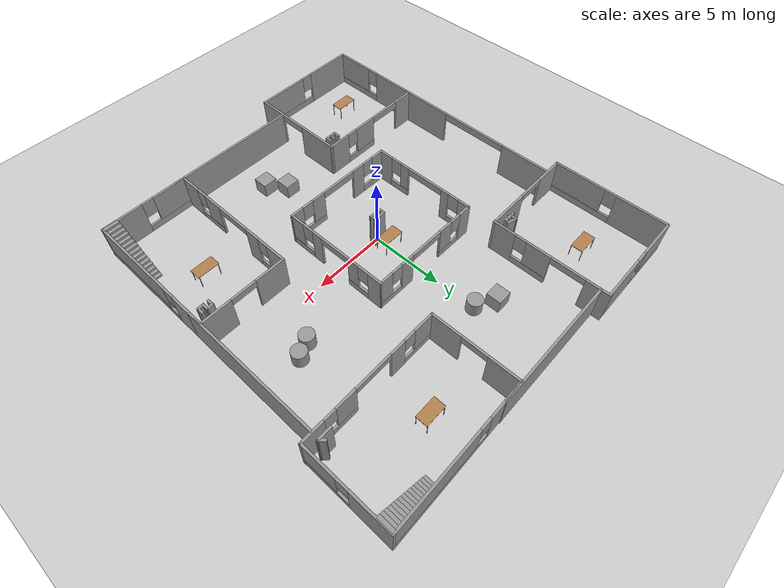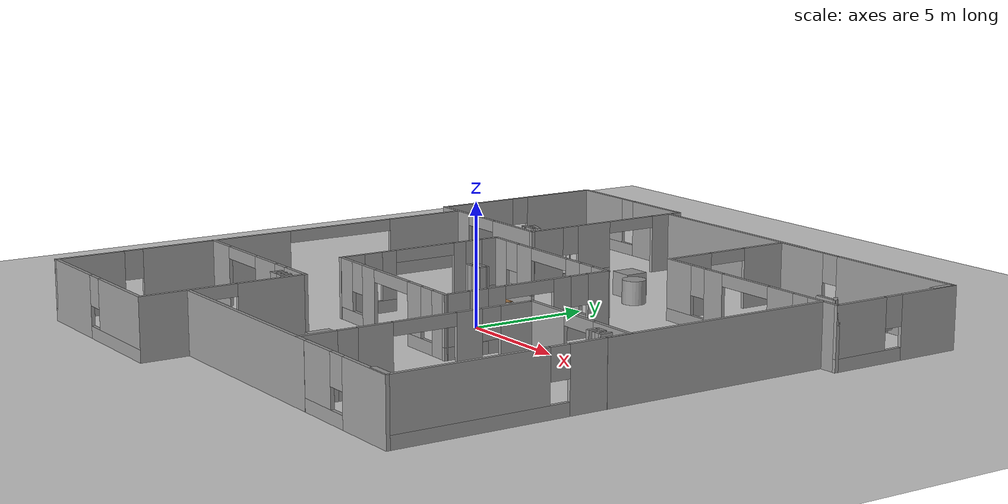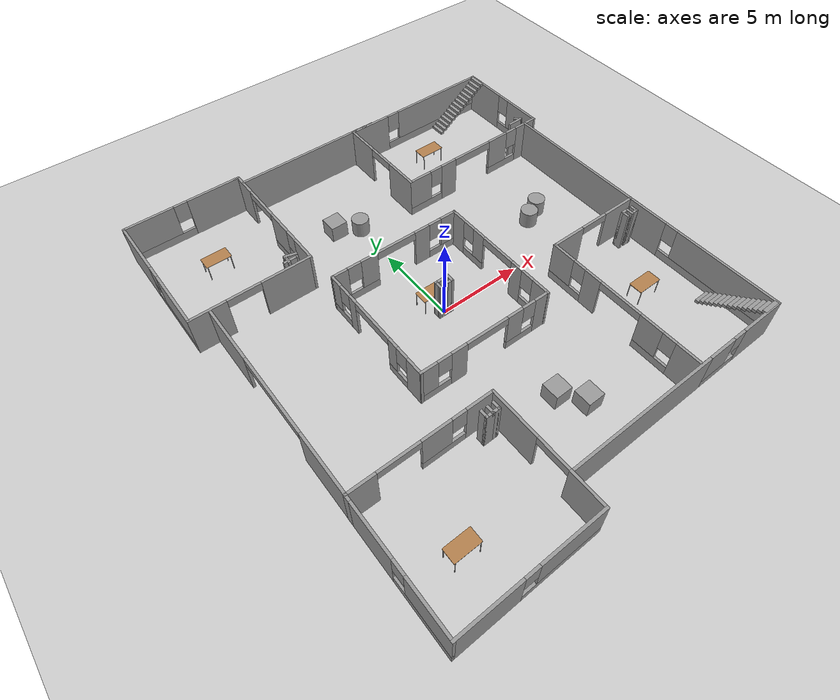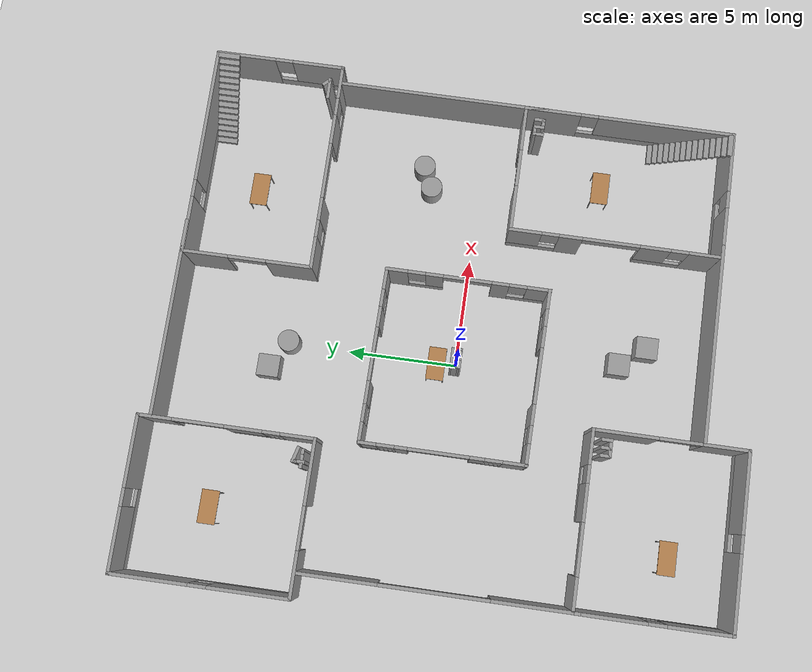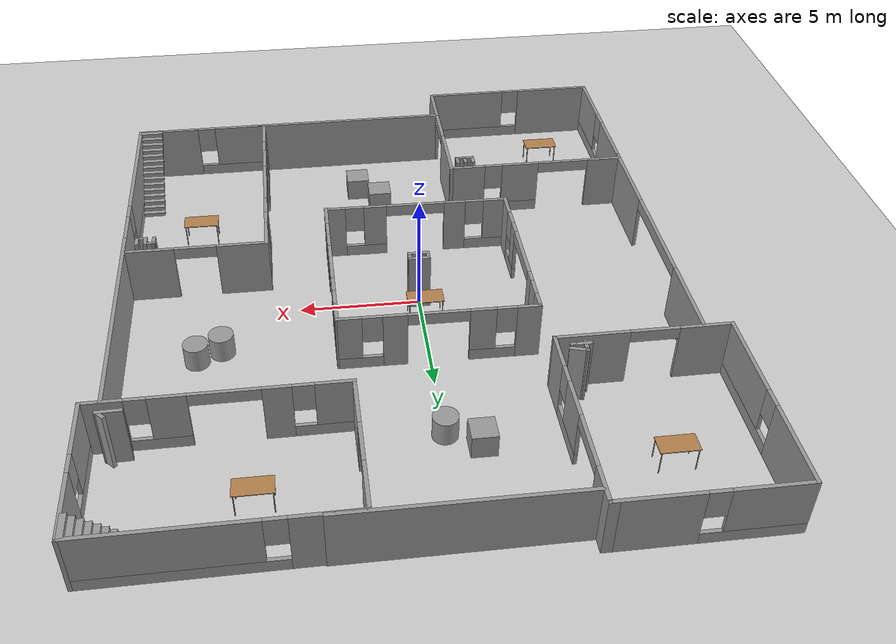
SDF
<sdf version="1.6">
 <world name="default">
  <light name="sun" type="directional">
   <pose>0 0 10 0 -0 0</pose>
   <diffuse>0.8 0.8 0.8 1</diffuse>
   <specular>0.2 0.2 0.2 1</specular>
   <attenuation>
    <range>1000</range>
    <constant>0.9</constant>
    <linear>0.01</linear>
    <quadratic>0.001</quadratic>
   </attenuation>
   <direction>-0.5 0.1 -0.9</direction>
  </light>
  <model name="ground_plane">
   <static>1</static>
   <link name="link">
    <collision name="collision">
     <geometry><plane><normal>0 0 1</normal><size>100 100</size></plane></geometry>
     <surface>
      <contact><collide_bitmask>65535</collide_bitmask></contact>
      <friction><ode><mu>100</mu><mu2>50</mu2></ode></friction>
     </surface>
    </collision>
    <visual name="visual">
     <cast_shadows>0</cast_shadows>
     <geometry><plane><normal>0 0 1</normal><size>100 100</size></plane></geometry>
     <material>
      <script><uri>file://media/materials/scripts/gazebo.material</uri><name>Gazebo/Grey</name></script>
     </material>
    </visual>
   </link>
  </model>
  <gravity>0 0 -9.8</gravity>
  <magnetic_field>6e-06 2.3e-05 -4.2e-05</magnetic_field>
  <atmosphere type="adiabatic"/>
  <physics name="default_physics" default="0" type="ode">
   <max_step_size>0.001</max_step_size>
   <real_time_factor>1</real_time_factor>
   <real_time_update_rate>1000</real_time_update_rate>
  </physics>
  <scene><ambient>0.4 0.4 0.4 1</ambient><background>0.7 0.7 0.7 1</background><shadows>1</shadows></scene>
  <audio><device>default</device></audio>
  <spherical_coordinates>
   <surface_model>EARTH_WGS84</surface_model>
   <latitude_deg>0</latitude_deg>
   <longitude_deg>0</longitude_deg>
   <elevation>0</elevation>
   <heading_deg>0</heading_deg>
  </spherical_coordinates>
  <model name="center">
   <pose>-0.31833 0.012222 0 0 -0 0</pose>
   <link name="Wall_0">
    <pose>-3.925 0.043311 0 0 -0 1.5708</pose>
    <visual name="Wall_0_Visual_0">
     <pose>-3.19646 0 1.25 0 -0 0</pose>
     <geometry><box><size>1.10708 0.15 2.5</size></box></geometry>
     <material>
      <script><uri>file://media/materials/scripts/gazebo.material</uri><name>Gazebo/Grey</name></script>
      <ambient>1 1 1 1</ambient>
     </material>
     <meta><layer>0</layer></meta>
    </visual>
    <collision name="Wall_0_Collision_0">
     <geometry><box><size>1.10708 0.15 2.5</size></box></geometry>
     <pose>-3.19646 0 1.25 0 -0 0</pose>
    </collision>
    <visual name="Wall_0_Visual_1">
     <pose>1.84852 0 1.25 0 -0 0</pose>
     <geometry><box><size>0.566695 0.15 2.5</size></box></geometry>
     <material>
      <script><uri>file://media/materials/scripts/gazebo.material</uri><name>Gazebo/Grey</name></script>
      <ambient>1 1 1 1</ambient>
     </material>
     <meta><layer>0</layer></meta>
    </visual>
    <collision name="Wall_0_Collision_1">
     <geometry><box><size>0.566695 0.15 2.5</size></box></geometry>
     <pose>1.84852 0 1.25 0 -0 0</pose>
    </collision>
    <visual name="Wall_0_Visual_2">
     <pose>-1.91585 0 0.25 0 -0 0</pose>
     <geometry><box><size>1.45415 0.15 0.5</size></box></geometry>
     <material>
      <script><uri>file://media/materials/scripts/gazebo.material</uri><name>Gazebo/Grey</name></script>
      <ambient>1 1 1 1</ambient>
     </material>
     <meta><layer>0</layer></meta>
    </visual>
    <collision name="Wall_0_Collision_2">
     <geometry><box><size>1.45415 0.15 0.5</size></box></geometry>
     <pose>-1.91585 0 0.25 0 -0 0</pose>
    </collision>
    <visual name="Wall_0_Visual_3">
     <pose>2.94093 0 0.25 0 -0 0</pose>
     <geometry><box><size>1.61813 0.15 0.5</size></box></geometry>
     <material>
      <script><uri>file://media/materials/scripts/gazebo.material</uri><name>Gazebo/Grey</name></script>
      <ambient>1 1 1 1</ambient>
     </material>
     <meta><layer>0</layer></meta>
    </visual>
    <collision name="Wall_0_Collision_3">
     <geometry><box><size>1.61813 0.15 0.5</size></box></geometry>
     <pose>2.94093 0 0.25 0 -0 0</pose>
    </collision>
    <visual name="Wall_0_Visual_4">
     <pose>-1.51585 0 1.5 0 -0 0</pose>
     <geometry><box><size>0.654145 0.15 2</size></box></geometry>
     <material>
      <script><uri>file://media/materials/scripts/gazebo.material</uri><name>Gazebo/Grey</name></script>
      <ambient>1 1 1 1</ambient>
     </material>
     <meta><layer>0</layer></meta>
    </visual>
    <collision name="Wall_0_Collision_4">
     <geometry><box><size>0.654145 0.15 2</size></box></geometry>
     <pose>-1.51585 0 1.5 0 -0 0</pose>
    </collision>
    <visual name="Wall_0_Visual_5">
     <pose>-1.51585 0 1.5 0 -0 0</pose>
     <geometry><box><size>0.654145 0.15 2</size></box></geometry>
     <material>
      <script><uri>file://media/materials/scripts/gazebo.material</uri><name>Gazebo/Grey</name></script>
      <ambient>1 1 1 1</ambient>
     </material>
     <meta><layer>0</layer></meta>
    </visual>
    <collision name="Wall_0_Collision_5">
     <geometry><box><size>0.654145 0.15 2</size></box></geometry>
     <pose>-1.51585 0 1.5 0 -0 0</pose>
    </collision>
    <visual name="Wall_0_Visual_6">
     <pose>3.34093 0 1.5 0 -0 0</pose>
     <geometry><box><size>0.818134 0.15 2</size></box></geometry>
     <material>
      <script><uri>file://media/materials/scripts/gazebo.material</uri><name>Gazebo/Grey</name></script>
      <ambient>1 1 1 1</ambient>
     </material>
     <meta><layer>0</layer></meta>
    </visual>
    <collision name="Wall_0_Collision_6">
     <geometry><box><size>0.818134 0.15 2</size></box></geometry>
     <pose>3.34093 0 1.5 0 -0 0</pose>
    </collision>
    <visual name="Wall_0_Visual_7">
     <pose>-2.24292 0 1.9 0 -0 0</pose>
     <geometry><box><size>0.8 0.15 1.2</size></box></geometry>
     <material>
      <script><uri>file://media/materials/scripts/gazebo.material</uri><name>Gazebo/Grey</name></script>
      <ambient>1 1 1 1</ambient>
     </material>
     <meta><layer>0</layer></meta>
    </visual>
    <collision name="Wall_0_Collision_7">
     <geometry><box><size>0.8 0.15 1.2</size></box></geometry>
     <pose>-2.24292 0 1.9 0 -0 0</pose>
    </collision>
    <visual name="Wall_0_Visual_8">
     <pose>2.53187 0 1.9 0 -0 0</pose>
     <geometry><box><size>0.8 0.15 1.2</size></box></geometry>
     <material>
      <script><uri>file://media/materials/scripts/gazebo.material</uri><name>Gazebo/Grey</name></script>
      <ambient>1 1 1 1</ambient>
     </material>
     <meta><layer>0</layer></meta>
    </visual>
    <collision name="Wall_0_Collision_8">
     <geometry><box><size>0.8 0.15 1.2</size></box></geometry>
     <pose>2.53187 0 1.9 0 -0 0</pose>
    </collision>
    <visual name="Wall_0_Visual_9">
     <pose>0.188198 0 2.25 0 -0 0</pose>
     <geometry><box><size>2.75395 0.15 0.5</size></box></geometry>
     <material>
      <script><uri>file://media/materials/scripts/gazebo.material</uri><name>Gazebo/Grey</name></script>
      <ambient>1 1 1 1</ambient>
     </material>
     <meta><layer>0</layer></meta>
    </visual>
    <collision name="Wall_0_Collision_9">
     <geometry><box><size>2.75395 0.15 0.5</size></box></geometry>
     <pose>0.188198 0 2.25 0 -0 0</pose>
    </collision>
    <visual name="Wall_0_Visual_10">
     <pose>0.188198 0 2.25 0 -0 0</pose>
     <geometry><box><size>2.75395 0.15 0.5</size></box></geometry>
     <material>
      <script><uri>file://media/materials/scripts/gazebo.material</uri><name>Gazebo/Grey</name></script>
      <ambient>1 1 1 1</ambient>
     </material>
     <meta><layer>0</layer></meta>
    </visual>
    <collision name="Wall_0_Collision_10">
     <geometry><box><size>2.75395 0.15 0.5</size></box></geometry>
     <pose>0.188198 0 2.25 0 -0 0</pose>
    </collision>
   </link>
   <link name="Wall_1">
    <pose>0 3.69208 0 0 -0 -0.01114</pose>
    <visual name="Wall_1_Visual_0">
     <pose>-3.51677 0 1.25 0 -0 0</pose>
     <geometry><box><size>0.966478 0.15 2.5</size></box></geometry>
     <material>
      <script><uri>file://media/materials/scripts/gazebo.material</uri><name>Gazebo/Grey</name></script>
      <ambient>1 1 1 1</ambient>
     </material>
     <meta><layer>0</layer></meta>
    </visual>
    <collision name="Wall_1_Collision_0">
     <geometry><box><size>0.966478 0.15 2.5</size></box></geometry>
     <pose>-3.51677 0 1.25 0 -0 0</pose>
    </collision>
    <visual name="Wall_1_Visual_1">
     <pose>1.70109 0 1.25 0 -0 0</pose>
     <geometry><box><size>0.951621 0.15 2.5</size></box></geometry>
     <material>
      <script><uri>file://media/materials/scripts/gazebo.material</uri><name>Gazebo/Grey</name></script>
      <ambient>1 1 1 1</ambient>
     </material>
     <meta><layer>0</layer></meta>
    </visual>
    <collision name="Wall_1_Collision_1">
     <geometry><box><size>0.951621 0.15 2.5</size></box></geometry>
     <pose>1.70109 0 1.25 0 -0 0</pose>
    </collision>
    <visual name="Wall_1_Visual_2">
     <pose>-2.11739 0 0.25 0 -0 0</pose>
     <geometry><box><size>1.8323 0.15 0.5</size></box></geometry>
     <material>
      <script><uri>file://media/materials/scripts/gazebo.material</uri><name>Gazebo/Grey</name></script>
      <ambient>1 1 1 1</ambient>
     </material>
     <meta><layer>0</layer></meta>
    </visual>
    <collision name="Wall_1_Collision_2">
     <geometry><box><size>1.8323 0.15 0.5</size></box></geometry>
     <pose>-2.11739 0 0.25 0 -0 0</pose>
    </collision>
    <visual name="Wall_1_Visual_3">
     <pose>3.08846 0 0.25 0 -0 0</pose>
     <geometry><box><size>1.8231 0.15 0.5</size></box></geometry>
     <material>
      <script><uri>file://media/materials/scripts/gazebo.material</uri><name>Gazebo/Grey</name></script>
      <ambient>1 1 1 1</ambient>
     </material>
     <meta><layer>0</layer></meta>
    </visual>
    <collision name="Wall_1_Collision_3">
     <geometry><box><size>1.8231 0.15 0.5</size></box></geometry>
     <pose>3.08846 0 0.25 0 -0 0</pose>
    </collision>
    <visual name="Wall_1_Visual_4">
     <pose>-1.71738 0 1.5 0 -0 0</pose>
     <geometry><box><size>1.03229 0.15 2</size></box></geometry>
     <material>
      <script><uri>file://media/materials/scripts/gazebo.material</uri><name>Gazebo/Grey</name></script>
      <ambient>1 1 1 1</ambient>
     </material>
     <meta><layer>0</layer></meta>
    </visual>
    <collision name="Wall_1_Collision_4">
     <geometry><box><size>1.03229 0.15 2</size></box></geometry>
     <pose>-1.71738 0 1.5 0 -0 0</pose>
    </collision>
    <visual name="Wall_1_Visual_5">
     <pose>-1.71738 0 1.5 0 -0 0</pose>
     <geometry><box><size>1.03229 0.15 2</size></box></geometry>
     <material>
      <script><uri>file://media/materials/scripts/gazebo.material</uri><name>Gazebo/Grey</name></script>
      <ambient>1 1 1 1</ambient>
     </material>
     <meta><layer>0</layer></meta>
    </visual>
    <collision name="Wall_1_Collision_5">
     <geometry><box><size>1.03229 0.15 2</size></box></geometry>
     <pose>-1.71738 0 1.5 0 -0 0</pose>
    </collision>
    <visual name="Wall_1_Visual_6">
     <pose>3.48846 0 1.5 0 -0 0</pose>
     <geometry><box><size>1.0231 0.15 2</size></box></geometry>
     <material>
      <script><uri>file://media/materials/scripts/gazebo.material</uri><name>Gazebo/Grey</name></script>
      <ambient>1 1 1 1</ambient>
     </material>
     <meta><layer>0</layer></meta>
    </visual>
    <collision name="Wall_1_Collision_6">
     <geometry><box><size>1.0231 0.15 2</size></box></geometry>
     <pose>3.48846 0 1.5 0 -0 0</pose>
    </collision>
    <visual name="Wall_1_Visual_7">
     <pose>-2.63353 0 1.9 0 -0 0</pose>
     <geometry><box><size>0.8 0.15 1.2</size></box></geometry>
     <material>
      <script><uri>file://media/materials/scripts/gazebo.material</uri><name>Gazebo/Grey</name></script>
      <ambient>1 1 1 1</ambient>
     </material>
     <meta><layer>0</layer></meta>
    </visual>
    <collision name="Wall_1_Collision_7">
     <geometry><box><size>0.8 0.15 1.2</size></box></geometry>
     <pose>-2.63353 0 1.9 0 -0 0</pose>
    </collision>
    <visual name="Wall_1_Visual_8">
     <pose>2.5769 0 1.9 0 -0 0</pose>
     <geometry><box><size>0.8 0.15 1.2</size></box></geometry>
     <material>
      <script><uri>file://media/materials/scripts/gazebo.material</uri><name>Gazebo/Grey</name></script>
      <ambient>1 1 1 1</ambient>
     </material>
     <meta><layer>0</layer></meta>
    </visual>
    <collision name="Wall_1_Collision_8">
     <geometry><box><size>0.8 0.15 1.2</size></box></geometry>
     <pose>2.5769 0 1.9 0 -0 0</pose>
    </collision>
    <visual name="Wall_1_Visual_9">
     <pose>0.012023 0 2.25 0 -0 0</pose>
     <geometry><box><size>2.42652 0.15 0.5</size></box></geometry>
     <material>
      <script><uri>file://media/materials/scripts/gazebo.material</uri><name>Gazebo/Grey</name></script>
      <ambient>1 1 1 1</ambient>
     </material>
     <meta><layer>0</layer></meta>
    </visual>
    <collision name="Wall_1_Collision_9">
     <geometry><box><size>2.42652 0.15 0.5</size></box></geometry>
     <pose>0.012023 0 2.25 0 -0 0</pose>
    </collision>
    <visual name="Wall_1_Visual_10">
     <pose>0.012023 0 2.25 0 -0 0</pose>
     <geometry><box><size>2.42652 0.15 0.5</size></box></geometry>
     <material>
      <script><uri>file://media/materials/scripts/gazebo.material</uri><name>Gazebo/Grey</name></script>
      <ambient>1 1 1 1</ambient>
     </material>
     <meta><layer>0</layer></meta>
    </visual>
    <collision name="Wall_1_Collision_10">
     <geometry><box><size>2.42652 0.15 0.5</size></box></geometry>
     <pose>0.012023 0 2.25 0 -0 0</pose>
    </collision>
   </link>
   <link name="Wall_2">
    <pose>3.925 -0.044139 0 0 -0 -1.5708</pose>
    <visual name="Wall_2_Visual_0">
     <pose>-3.25348 0 1.25 0 -0 0</pose>
     <geometry><box><size>1.02801 0.15 2.5</size></box></geometry>
     <material>
      <script><uri>file://media/materials/scripts/gazebo.material</uri><name>Gazebo/Grey</name></script>
      <ambient>1 1 1 1</ambient>
     </material>
     <meta><layer>0</layer></meta>
    </visual>
    <collision name="Wall_2_Collision_0">
     <geometry><box><size>1.02801 0.15 2.5</size></box></geometry>
     <pose>-3.25348 0 1.25 0 -0 0</pose>
    </collision>
    <visual name="Wall_2_Visual_1">
     <pose>1.45026 0 1.25 0 -0 0</pose>
     <geometry><box><size>0.785321 0.15 2.5</size></box></geometry>
     <material>
      <script><uri>file://media/materials/scripts/gazebo.material</uri><name>Gazebo/Grey</name></script>
      <ambient>1 1 1 1</ambient>
     </material>
     <meta><layer>0</layer></meta>
    </visual>
    <collision name="Wall_2_Collision_1">
     <geometry><box><size>0.785321 0.15 2.5</size></box></geometry>
     <pose>1.45026 0 1.25 0 -0 0</pose>
    </collision>
    <visual name="Wall_2_Visual_2">
     <pose>-1.93807 0 0.25 0 -0 0</pose>
     <geometry><box><size>1.60281 0.15 0.5</size></box></geometry>
     <material>
      <script><uri>file://media/materials/scripts/gazebo.material</uri><name>Gazebo/Grey</name></script>
      <ambient>1 1 1 1</ambient>
     </material>
     <meta><layer>0</layer></meta>
    </visual>
    <collision name="Wall_2_Collision_2">
     <geometry><box><size>1.60281 0.15 0.5</size></box></geometry>
     <pose>-1.93807 0 0.25 0 -0 0</pose>
    </collision>
    <visual name="Wall_2_Visual_3">
     <pose>2.80521 0 0.25 0 -0 0</pose>
     <geometry><box><size>1.92457 0.15 0.5</size></box></geometry>
     <material>
      <script><uri>file://media/materials/scripts/gazebo.material</uri><name>Gazebo/Grey</name></script>
      <ambient>1 1 1 1</ambient>
     </material>
     <meta><layer>0</layer></meta>
    </visual>
    <collision name="Wall_2_Collision_3">
     <geometry><box><size>1.92457 0.15 0.5</size></box></geometry>
     <pose>2.80521 0 0.25 0 -0 0</pose>
    </collision>
    <visual name="Wall_2_Visual_4">
     <pose>-1.53807 0 1.5 0 -0 0</pose>
     <geometry><box><size>0.802811 0.15 2</size></box></geometry>
     <material>
      <script><uri>file://media/materials/scripts/gazebo.material</uri><name>Gazebo/Grey</name></script>
      <ambient>1 1 1 1</ambient>
     </material>
     <meta><layer>0</layer></meta>
    </visual>
    <collision name="Wall_2_Collision_4">
     <geometry><box><size>0.802811 0.15 2</size></box></geometry>
     <pose>-1.53807 0 1.5 0 -0 0</pose>
    </collision>
    <visual name="Wall_2_Visual_5">
     <pose>-1.53807 0 1.5 0 -0 0</pose>
     <geometry><box><size>0.802811 0.15 2</size></box></geometry>
     <material>
      <script><uri>file://media/materials/scripts/gazebo.material</uri><name>Gazebo/Grey</name></script>
      <ambient>1 1 1 1</ambient>
     </material>
     <meta><layer>0</layer></meta>
    </visual>
    <collision name="Wall_2_Collision_5">
     <geometry><box><size>0.802811 0.15 2</size></box></geometry>
     <pose>-1.53807 0 1.5 0 -0 0</pose>
    </collision>
    <visual name="Wall_2_Visual_6">
     <pose>3.20521 0 1.5 0 -0 0</pose>
     <geometry><box><size>1.12457 0.15 2</size></box></geometry>
     <material>
      <script><uri>file://media/materials/scripts/gazebo.material</uri><name>Gazebo/Grey</name></script>
      <ambient>1 1 1 1</ambient>
     </material>
     <meta><layer>0</layer></meta>
    </visual>
    <collision name="Wall_2_Collision_6">
     <geometry><box><size>1.12457 0.15 2</size></box></geometry>
     <pose>3.20521 0 1.5 0 -0 0</pose>
    </collision>
    <visual name="Wall_2_Visual_7">
     <pose>-2.33948 0 1.9 0 -0 0</pose>
     <geometry><box><size>0.8 0.15 1.2</size></box></geometry>
     <material>
      <script><uri>file://media/materials/scripts/gazebo.material</uri><name>Gazebo/Grey</name></script>
      <ambient>1 1 1 1</ambient>
     </material>
     <meta><layer>0</layer></meta>
    </visual>
    <collision name="Wall_2_Collision_7">
     <geometry><box><size>0.8 0.15 1.2</size></box></geometry>
     <pose>-2.33948 0 1.9 0 -0 0</pose>
    </collision>
    <visual name="Wall_2_Visual_8">
     <pose>2.24292 0 1.9 0 -0 0</pose>
     <geometry><box><size>0.8 0.15 1.2</size></box></geometry>
     <material>
      <script><uri>file://media/materials/scripts/gazebo.material</uri><name>Gazebo/Grey</name></script>
      <ambient>1 1 1 1</ambient>
     </material>
     <meta><layer>0</layer></meta>
    </visual>
    <collision name="Wall_2_Collision_8">
     <geometry><box><size>0.8 0.15 1.2</size></box></geometry>
     <pose>2.24292 0 1.9 0 -0 0</pose>
    </collision>
    <visual name="Wall_2_Visual_9">
     <pose>-0.039532 0 2.25 0 -0 0</pose>
     <geometry><box><size>2.19427 0.15 0.5</size></box></geometry>
     <material>
      <script><uri>file://media/materials/scripts/gazebo.material</uri><name>Gazebo/Grey</name></script>
      <ambient>1 1 1 1</ambient>
     </material>
     <meta><layer>0</layer></meta>
    </visual>
    <collision name="Wall_2_Collision_9">
     <geometry><box><size>2.19427 0.15 0.5</size></box></geometry>
     <pose>-0.039532 0 2.25 0 -0 0</pose>
    </collision>
    <visual name="Wall_2_Visual_10">
     <pose>-0.039532 0 2.25 0 -0 0</pose>
     <geometry><box><size>2.19427 0.15 0.5</size></box></geometry>
     <material>
      <script><uri>file://media/materials/scripts/gazebo.material</uri><name>Gazebo/Grey</name></script>
      <ambient>1 1 1 1</ambient>
     </material>
     <meta><layer>0</layer></meta>
    </visual>
    <collision name="Wall_2_Collision_10">
     <geometry><box><size>2.19427 0.15 0.5</size></box></geometry>
     <pose>-0.039532 0 2.25 0 -0 0</pose>
    </collision>
   </link>
   <link name="Wall_3">
    <pose>0 -3.66667 0 0 -0 3.12823</pose>
    <visual name="Wall_3_Visual_0">
     <pose>-3.54389 0 1.25 0 -0 0</pose>
     <geometry><box><size>0.912232 0.15 2.5</size></box></geometry>
     <material>
      <script><uri>file://media/materials/scripts/gazebo.material</uri><name>Gazebo/Grey</name></script>
      <ambient>1 1 1 1</ambient>
     </material>
     <meta><layer>0</layer></meta>
    </visual>
    <collision name="Wall_3_Collision_0">
     <geometry><box><size>0.912232 0.15 2.5</size></box></geometry>
     <pose>-3.54389 0 1.25 0 -0 0</pose>
    </collision>
    <visual name="Wall_3_Visual_1">
     <pose>1.68912 0 1.25 0 -0 0</pose>
     <geometry><box><size>0.942104 0.15 2.5</size></box></geometry>
     <material>
      <script><uri>file://media/materials/scripts/gazebo.material</uri><name>Gazebo/Grey</name></script>
      <ambient>1 1 1 1</ambient>
     </material>
     <meta><layer>0</layer></meta>
    </visual>
    <collision name="Wall_3_Collision_1">
     <geometry><box><size>0.942104 0.15 2.5</size></box></geometry>
     <pose>1.68912 0 1.25 0 -0 0</pose>
    </collision>
    <visual name="Wall_3_Visual_2">
     <pose>-2.1983 0 0.25 0 -0 0</pose>
     <geometry><box><size>1.77895 0.15 0.5</size></box></geometry>
     <material>
      <script><uri>file://media/materials/scripts/gazebo.material</uri><name>Gazebo/Grey</name></script>
      <ambient>1 1 1 1</ambient>
     </material>
     <meta><layer>0</layer></meta>
    </visual>
    <collision name="Wall_3_Collision_2">
     <geometry><box><size>1.77895 0.15 0.5</size></box></geometry>
     <pose>-2.1983 0 0.25 0 -0 0</pose>
    </collision>
    <visual name="Wall_3_Visual_3">
     <pose>3.08009 0 0.25 0 -0 0</pose>
     <geometry><box><size>1.83984 0.15 0.5</size></box></geometry>
     <material>
      <script><uri>file://media/materials/scripts/gazebo.material</uri><name>Gazebo/Grey</name></script>
      <ambient>1 1 1 1</ambient>
     </material>
     <meta><layer>0</layer></meta>
    </visual>
    <collision name="Wall_3_Collision_3">
     <geometry><box><size>1.83984 0.15 0.5</size></box></geometry>
     <pose>3.08009 0 0.25 0 -0 0</pose>
    </collision>
    <visual name="Wall_3_Visual_4">
     <pose>-1.7983 0 1.5 0 -0 0</pose>
     <geometry><box><size>0.978951 0.15 2</size></box></geometry>
     <material>
      <script><uri>file://media/materials/scripts/gazebo.material</uri><name>Gazebo/Grey</name></script>
      <ambient>1 1 1 1</ambient>
     </material>
     <meta><layer>0</layer></meta>
    </visual>
    <collision name="Wall_3_Collision_4">
     <geometry><box><size>0.978951 0.15 2</size></box></geometry>
     <pose>-1.7983 0 1.5 0 -0 0</pose>
    </collision>
    <visual name="Wall_3_Visual_5">
     <pose>-1.7983 0 1.5 0 -0 0</pose>
     <geometry><box><size>0.978951 0.15 2</size></box></geometry>
     <material>
      <script><uri>file://media/materials/scripts/gazebo.material</uri><name>Gazebo/Grey</name></script>
      <ambient>1 1 1 1</ambient>
     </material>
     <meta><layer>0</layer></meta>
    </visual>
    <collision name="Wall_3_Collision_5">
     <geometry><box><size>0.978951 0.15 2</size></box></geometry>
     <pose>-1.7983 0 1.5 0 -0 0</pose>
    </collision>
    <visual name="Wall_3_Visual_6">
     <pose>3.48009 0 1.5 0 -0 0</pose>
     <geometry><box><size>1.03984 0.15 2</size></box></geometry>
     <material>
      <script><uri>file://media/materials/scripts/gazebo.material</uri><name>Gazebo/Grey</name></script>
      <ambient>1 1 1 1</ambient>
     </material>
     <meta><layer>0</layer></meta>
    </visual>
    <collision name="Wall_3_Collision_6">
     <geometry><box><size>1.03984 0.15 2</size></box></geometry>
     <pose>3.48009 0 1.5 0 -0 0</pose>
    </collision>
    <visual name="Wall_3_Visual_7">
     <pose>-2.68778 0 1.9 0 -0 0</pose>
     <geometry><box><size>0.8 0.15 1.2</size></box></geometry>
     <material>
      <script><uri>file://media/materials/scripts/gazebo.material</uri><name>Gazebo/Grey</name></script>
      <ambient>1 1 1 1</ambient>
     </material>
     <meta><layer>0</layer></meta>
    </visual>
    <collision name="Wall_3_Collision_7">
     <geometry><box><size>0.8 0.15 1.2</size></box></geometry>
     <pose>-2.68778 0 1.9 0 -0 0</pose>
    </collision>
    <visual name="Wall_3_Visual_8">
     <pose>2.56018 0 1.9 0 -0 0</pose>
     <geometry><box><size>0.8 0.15 1.2</size></box></geometry>
     <material>
      <script><uri>file://media/materials/scripts/gazebo.material</uri><name>Gazebo/Grey</name></script>
      <ambient>1 1 1 1</ambient>
     </material>
     <meta><layer>0</layer></meta>
    </visual>
    <collision name="Wall_3_Collision_8">
     <geometry><box><size>0.8 0.15 1.2</size></box></geometry>
     <pose>2.56018 0 1.9 0 -0 0</pose>
    </collision>
    <visual name="Wall_3_Visual_9">
     <pose>-0.045378 0 2.25 0 -0 0</pose>
     <geometry><box><size>2.5269 0.15 0.5</size></box></geometry>
     <material>
      <script><uri>file://media/materials/scripts/gazebo.material</uri><name>Gazebo/Grey</name></script>
      <ambient>1 1 1 1</ambient>
     </material>
     <meta><layer>0</layer></meta>
    </visual>
    <collision name="Wall_3_Collision_9">
     <geometry><box><size>2.5269 0.15 0.5</size></box></geometry>
     <pose>-0.045378 0 2.25 0 -0 0</pose>
    </collision>
    <visual name="Wall_3_Visual_10">
     <pose>-0.045378 0 2.25 0 -0 0</pose>
     <geometry><box><size>2.5269 0.15 0.5</size></box></geometry>
     <material>
      <script><uri>file://media/materials/scripts/gazebo.material</uri><name>Gazebo/Grey</name></script>
      <ambient>1 1 1 1</ambient>
     </material>
     <meta><layer>0</layer></meta>
    </visual>
    <collision name="Wall_3_Collision_10">
     <geometry><box><size>2.5269 0.15 0.5</size></box></geometry>
     <pose>-0.045378 0 2.25 0 -0 0</pose>
    </collision>
   </link>
   <static>1</static>
  </model>
  <model name="house3">
   <pose>-6.19988 -9.75215 0 0 -0 0</pose>
   <link name="Wall_3">
    <pose>-0 3.425 0 0 -0 3.14159</pose>
    <visual name="Wall_3_Visual_0">
     <pose>-3.18921 0 1.25 0 -0 0</pose>
     <geometry><box><size>1.62157 0.15 2.5</size></box></geometry>
     <material>
      <script><uri>file://media/materials/scripts/gazebo.material</uri><name>Gazebo/Grey</name></script>
      <ambient>1 1 1 1</ambient>
     </material>
     <meta><layer>0</layer></meta>
    </visual>
    <collision name="Wall_3_Collision_0">
     <geometry><box><size>1.62157 0.15 2.5</size></box></geometry>
     <pose>-3.18921 0 1.25 0 -0 0</pose>
    </collision>
    <visual name="Wall_3_Visual_1">
     <pose>3.20799 0 1.25 0 -0 0</pose>
     <geometry><box><size>1.58401 0.15 2.5</size></box></geometry>
     <material>
      <script><uri>file://media/materials/scripts/gazebo.material</uri><name>Gazebo/Grey</name></script>
      <ambient>1 1 1 1</ambient>
     </material>
     <meta><layer>0</layer></meta>
    </visual>
    <collision name="Wall_3_Collision_1">
     <geometry><box><size>1.58401 0.15 2.5</size></box></geometry>
     <pose>3.20799 0 1.25 0 -0 0</pose>
    </collision>
    <visual name="Wall_3_Visual_2">
     <pose>-1.13919 0 0.25 0 -0 0</pose>
     <geometry><box><size>2.47847 0.15 0.5</size></box></geometry>
     <material>
      <script><uri>file://media/materials/scripts/gazebo.material</uri><name>Gazebo/Grey</name></script>
      <ambient>1 1 1 1</ambient>
     </material>
     <meta><layer>0</layer></meta>
    </visual>
    <collision name="Wall_3_Collision_2">
     <geometry><box><size>2.47847 0.15 0.5</size></box></geometry>
     <pose>-1.13919 0 0.25 0 -0 0</pose>
    </collision>
    <visual name="Wall_3_Visual_3">
     <pose>-0.739193 0 1.5 0 -0 0</pose>
     <geometry><box><size>1.67847 0.15 2</size></box></geometry>
     <material>
      <script><uri>file://media/materials/scripts/gazebo.material</uri><name>Gazebo/Grey</name></script>
      <ambient>1 1 1 1</ambient>
     </material>
     <meta><layer>0</layer></meta>
    </visual>
    <collision name="Wall_3_Collision_3">
     <geometry><box><size>1.67847 0.15 2</size></box></geometry>
     <pose>-0.739193 0 1.5 0 -0 0</pose>
    </collision>
    <visual name="Wall_3_Visual_4">
     <pose>-1.97843 0 1.9 0 -0 0</pose>
     <geometry><box><size>0.8 0.15 1.2</size></box></geometry>
     <material>
      <script><uri>file://media/materials/scripts/gazebo.material</uri><name>Gazebo/Grey</name></script>
      <ambient>1 1 1 1</ambient>
     </material>
     <meta><layer>0</layer></meta>
    </visual>
    <collision name="Wall_3_Collision_4">
     <geometry><box><size>0.8 0.15 1.2</size></box></geometry>
     <pose>-1.97843 0 1.9 0 -0 0</pose>
    </collision>
    <visual name="Wall_3_Visual_5">
     <pose>1.25802 0 2.25 0 -0 0</pose>
     <geometry><box><size>2.31595 0.15 0.5</size></box></geometry>
     <material>
      <script><uri>file://media/materials/scripts/gazebo.material</uri><name>Gazebo/Grey</name></script>
      <ambient>1 1 1 1</ambient>
     </material>
     <meta><layer>0</layer></meta>
    </visual>
    <collision name="Wall_3_Collision_5">
     <geometry><box><size>2.31595 0.15 0.5</size></box></geometry>
     <pose>1.25802 0 2.25 0 -0 0</pose>
    </collision>
   </link>
   <link name="Wall_4">
    <collision name="Wall_4_Collision">
     <geometry><box><size>0.4 0.15 2.5</size></box></geometry>
     <pose>0 0 1.25 0 -0 0</pose>
    </collision>
    <visual name="Wall_4_Visual">
     <pose>0 0 1.25 0 -0 0</pose>
     <geometry><box><size>0.4 0.15 2.5</size></box></geometry>
     <material>
      <script><uri>file://media/materials/scripts/gazebo.material</uri><name>Gazebo/Grey</name></script>
      <ambient>1 1 1 1</ambient>
     </material>
     <meta><layer>0</layer></meta>
    </visual>
    <pose>-3.925 3.3 0 0 -0 -1.5708</pose>
   </link>
   <link name="Wall_6">
    <pose>-3.925 0 0 0 -0 -1.5708</pose>
    <visual name="Wall_6_Visual_0">
     <pose>-1.85783 0 1.25 0 -0 0</pose>
     <geometry><box><size>3.28434 0.15 2.5</size></box></geometry>
     <material>
      <script><uri>file://media/materials/scripts/gazebo.material</uri><name>Gazebo/Grey</name></script>
      <ambient>1 1 1 1</ambient>
     </material>
     <meta><layer>0</layer></meta>
    </visual>
    <collision name="Wall_6_Collision_0">
     <geometry><box><size>3.28434 0.15 2.5</size></box></geometry>
     <pose>-1.85783 0 1.25 0 -0 0</pose>
    </collision>
    <visual name="Wall_6_Visual_1">
     <pose>1.64217 0 0.25 0 -0 0</pose>
     <geometry><box><size>3.71566 0.15 0.5</size></box></geometry>
     <material>
      <script><uri>file://media/materials/scripts/gazebo.material</uri><name>Gazebo/Grey</name></script>
      <ambient>1 1 1 1</ambient>
     </material>
     <meta><layer>0</layer></meta>
    </visual>
    <collision name="Wall_6_Collision_1">
     <geometry><box><size>3.71566 0.15 0.5</size></box></geometry>
     <pose>1.64217 0 0.25 0 -0 0</pose>
    </collision>
    <visual name="Wall_6_Visual_2">
     <pose>2.04217 0 1.5 0 -0 0</pose>
     <geometry><box><size>2.91566 0.15 2</size></box></geometry>
     <material>
      <script><uri>file://media/materials/scripts/gazebo.material</uri><name>Gazebo/Grey</name></script>
      <ambient>1 1 1 1</ambient>
     </material>
     <meta><layer>0</layer></meta>
    </visual>
    <collision name="Wall_6_Collision_2">
     <geometry><box><size>2.91566 0.15 2</size></box></geometry>
     <pose>2.04217 0 1.5 0 -0 0</pose>
    </collision>
    <visual name="Wall_6_Visual_3">
     <pose>0.18434 0 1.9 0 -0 0</pose>
     <geometry><box><size>0.8 0.15 1.2</size></box></geometry>
     <material>
      <script><uri>file://media/materials/scripts/gazebo.material</uri><name>Gazebo/Grey</name></script>
      <ambient>1 1 1 1</ambient>
     </material>
     <meta><layer>0</layer></meta>
    </visual>
    <collision name="Wall_6_Collision_3">
     <geometry><box><size>0.8 0.15 1.2</size></box></geometry>
     <pose>0.18434 0 1.9 0 -0 0</pose>
    </collision>
   </link>
   <link name="Wall_7">
    <pose>-0 -3.425 0 0 -0 0</pose>
    <visual name="Wall_7_Visual_0">
     <pose>-2.2424 0 1.25 0 -0 0</pose>
     <geometry><box><size>3.51519 0.15 2.5</size></box></geometry>
     <material>
      <script><uri>file://media/materials/scripts/gazebo.material</uri><name>Gazebo/Grey</name></script>
      <ambient>1 1 1 1</ambient>
     </material>
     <meta><layer>0</layer></meta>
    </visual>
    <collision name="Wall_7_Collision_0">
     <geometry><box><size>3.51519 0.15 2.5</size></box></geometry>
     <pose>-2.2424 0 1.25 0 -0 0</pose>
    </collision>
    <visual name="Wall_7_Visual_1">
     <pose>1.7576 0 0.25 0 -0 0</pose>
     <geometry><box><size>4.4848 0.15 0.5</size></box></geometry>
     <material>
      <script><uri>file://media/materials/scripts/gazebo.material</uri><name>Gazebo/Grey</name></script>
      <ambient>1 1 1 1</ambient>
     </material>
     <meta><layer>0</layer></meta>
    </visual>
    <collision name="Wall_7_Collision_1">
     <geometry><box><size>4.4848 0.15 0.5</size></box></geometry>
     <pose>1.7576 0 0.25 0 -0 0</pose>
    </collision>
    <visual name="Wall_7_Visual_2">
     <pose>2.1576 0 1.5 0 -0 0</pose>
     <geometry><box><size>3.6848 0.15 2</size></box></geometry>
     <material>
      <script><uri>file://media/materials/scripts/gazebo.material</uri><name>Gazebo/Grey</name></script>
      <ambient>1 1 1 1</ambient>
     </material>
     <meta><layer>0</layer></meta>
    </visual>
    <collision name="Wall_7_Collision_2">
     <geometry><box><size>3.6848 0.15 2</size></box></geometry>
     <pose>2.1576 0 1.5 0 -0 0</pose>
    </collision>
    <visual name="Wall_7_Visual_3">
     <pose>-0.084805 0 1.9 0 -0 0</pose>
     <geometry><box><size>0.8 0.15 1.2</size></box></geometry>
     <material>
      <script><uri>file://media/materials/scripts/gazebo.material</uri><name>Gazebo/Grey</name></script>
      <ambient>1 1 1 1</ambient>
     </material>
     <meta><layer>0</layer></meta>
    </visual>
    <collision name="Wall_7_Collision_3">
     <geometry><box><size>0.8 0.15 1.2</size></box></geometry>
     <pose>-0.084805 0 1.9 0 -0 0</pose>
    </collision>
   </link>
   <link name="Wall_8">
    <pose>3.925 0 0 0 -0 1.5708</pose>
    <visual name="Wall_8_Visual_0">
     <pose>-2.44138 0 1.25 0 -0 0</pose>
     <geometry><box><size>2.11723 0.15 2.5</size></box></geometry>
     <material>
      <script><uri>file://media/materials/scripts/gazebo.material</uri><name>Gazebo/Grey</name></script>
      <ambient>1 1 1 1</ambient>
     </material>
     <meta><layer>0</layer></meta>
    </visual>
    <collision name="Wall_8_Collision_0">
     <geometry><box><size>2.11723 0.15 2.5</size></box></geometry>
     <pose>-2.44138 0 1.25 0 -0 0</pose>
    </collision>
    <visual name="Wall_8_Visual_1">
     <pose>2.01431 0 1.25 0 -0 0</pose>
     <geometry><box><size>2.97138 0.15 2.5</size></box></geometry>
     <material>
      <script><uri>file://media/materials/scripts/gazebo.material</uri><name>Gazebo/Grey</name></script>
      <ambient>1 1 1 1</ambient>
     </material>
     <meta><layer>0</layer></meta>
    </visual>
    <collision name="Wall_8_Collision_1">
     <geometry><box><size>2.97138 0.15 2.5</size></box></geometry>
     <pose>2.01431 0 1.25 0 -0 0</pose>
    </collision>
    <visual name="Wall_8_Visual_2">
     <pose>-0.427073 0 2.25 0 -0 0</pose>
     <geometry><box><size>1.91139 0.15 0.5</size></box></geometry>
     <material>
      <script><uri>file://media/materials/scripts/gazebo.material</uri><name>Gazebo/Grey</name></script>
      <ambient>1 1 1 1</ambient>
     </material>
     <meta><layer>0</layer></meta>
    </visual>
    <collision name="Wall_8_Collision_2">
     <geometry><box><size>1.91139 0.15 0.5</size></box></geometry>
     <pose>-0.427073 0 2.25 0 -0 0</pose>
    </collision>
   </link>
   <static>1</static>
  </model>
  <model name="t2_1">
   <pose>-10.117 -0.381007 0 0 -0 0</pose>
   <link name="Wall_0">
    <pose>0 0 0 0 -0 1.5708</pose>
    <visual name="Wall_0_Visual_0">
     <pose>-4.21611 0 1.25 0 -0 0</pose>
     <geometry><box><size>3.56778 0.15 2.5</size></box></geometry>
     <material>
      <script><uri>file://media/materials/scripts/gazebo.material</uri><name>Gazebo/Grey</name></script>
      <ambient>1 1 1 1</ambient>
     </material>
     <meta><layer>0</layer></meta>
    </visual>
    <collision name="Wall_0_Collision_0">
     <geometry><box><size>3.56778 0.15 2.5</size></box></geometry>
     <pose>-4.21611 0 1.25 0 -0 0</pose>
    </collision>
    <visual name="Wall_0_Visual_1">
     <pose>4.22149 0 1.25 0 -0 0</pose>
     <geometry><box><size>3.55702 0.15 2.5</size></box></geometry>
     <material>
      <script><uri>file://media/materials/scripts/gazebo.material</uri><name>Gazebo/Grey</name></script>
      <ambient>1 1 1 1</ambient>
     </material>
     <meta><layer>0</layer></meta>
    </visual>
    <collision name="Wall_0_Collision_1">
     <geometry><box><size>3.55702 0.15 2.5</size></box></geometry>
     <pose>4.22149 0 1.25 0 -0 0</pose>
    </collision>
    <visual name="Wall_0_Visual_2">
     <pose>0.005377 0 2.25 0 -0 0</pose>
     <geometry><box><size>4.8752 0.15 0.5</size></box></geometry>
     <material>
      <script><uri>file://media/materials/scripts/gazebo.material</uri><name>Gazebo/Grey</name></script>
      <ambient>1 1 1 1</ambient>
     </material>
     <meta><layer>0</layer></meta>
    </visual>
    <collision name="Wall_0_Collision_2">
     <geometry><box><size>4.8752 0.15 0.5</size></box></geometry>
     <pose>0.005377 0 2.25 0 -0 0</pose>
    </collision>
   </link>
   <static>1</static>
  </model>
  <model name="t1">
   <pose>2.28112 -11.2146 0 0 -0 0</pose>
   <link name="Wall_7">
    <collision name="Wall_7_Collision">
     <geometry><box><size>9 0.15 2.5</size></box></geometry>
     <pose>0 0 1.25 0 -0 0</pose>
    </collision>
    <visual name="Wall_7_Visual">
     <pose>0 0 1.25 0 -0 0</pose>
     <geometry><box><size>9 0.15 2.5</size></box></geometry>
     <material>
      <script><uri>file://media/materials/scripts/gazebo.material</uri><name>Gazebo/Grey</name></script>
      <ambient>1 1 1 1</ambient>
     </material>
     <meta><layer>0</layer></meta>
    </visual>
   </link>
   <static>1</static>
  </model>
  <model name="house1">
   <pose>9.11824 -6.41072 0 0 -0 0</pose>
   <link name="Stairs_0">
    <visual name="Stairs_0_Visual_0">
     <pose>2.40484 -1.42237 0.083333 0 -0 0</pose>
     <geometry><box><size>1 0.233333 0.166667</size></box></geometry>
     <material>
      <script><uri>file://media/materials/scripts/gazebo.material</uri><name>Gazebo/Grey</name></script>
      <ambient>1 1 1 1</ambient>
     </material>
     <meta><layer>0</layer></meta>
    </visual>
    <collision name="Stairs_0_Collision_0">
     <geometry><box><size>1 0.233333 0.166667</size></box></geometry>
     <pose>2.40484 -1.42237 0.083333 0 -0 0</pose>
    </collision>
    <visual name="Stairs_0_Visual_1">
     <pose>2.40484 -1.6557 0.25 0 -0 0</pose>
     <geometry><box><size>1 0.233333 0.166667</size></box></geometry>
     <material>
      <script><uri>file://media/materials/scripts/gazebo.material</uri><name>Gazebo/Grey</name></script>
      <ambient>1 1 1 1</ambient>
     </material>
     <meta><layer>0</layer></meta>
    </visual>
    <collision name="Stairs_0_Collision_1">
     <geometry><box><size>1 0.233333 0.166667</size></box></geometry>
     <pose>2.40484 -1.6557 0.25 0 -0 0</pose>
    </collision>
    <visual name="Stairs_0_Visual_2">
     <pose>2.40484 -1.88904 0.416667 0 -0 0</pose>
     <geometry><box><size>1 0.233333 0.166667</size></box></geometry>
     <material>
      <script><uri>file://media/materials/scripts/gazebo.material</uri><name>Gazebo/Grey</name></script>
      <ambient>1 1 1 1</ambient>
     </material>
     <meta><layer>0</layer></meta>
    </visual>
    <collision name="Stairs_0_Collision_2">
     <geometry><box><size>1 0.233333 0.166667</size></box></geometry>
     <pose>2.40484 -1.88904 0.416667 0 -0 0</pose>
    </collision>
    <visual name="Stairs_0_Visual_3">
     <pose>2.40484 -2.12237 0.583333 0 -0 0</pose>
     <geometry><box><size>1 0.233333 0.166667</size></box></geometry>
     <material>
      <script><uri>file://media/materials/scripts/gazebo.material</uri><name>Gazebo/Grey</name></script>
      <ambient>1 1 1 1</ambient>
     </material>
     <meta><layer>0</layer></meta>
    </visual>
    <collision name="Stairs_0_Collision_3">
     <geometry><box><size>1 0.233333 0.166667</size></box></geometry>
     <pose>2.40484 -2.12237 0.583333 0 -0 0</pose>
    </collision>
    <visual name="Stairs_0_Visual_4">
     <pose>2.40484 -2.3557 0.75 0 -0 0</pose>
     <geometry><box><size>1 0.233333 0.166667</size></box></geometry>
     <material>
      <script><uri>file://media/materials/scripts/gazebo.material</uri><name>Gazebo/Grey</name></script>
      <ambient>1 1 1 1</ambient>
     </material>
     <meta><layer>0</layer></meta>
    </visual>
    <collision name="Stairs_0_Collision_4">
     <geometry><box><size>1 0.233333 0.166667</size></box></geometry>
     <pose>2.40484 -2.3557 0.75 0 -0 0</pose>
    </collision>
    <visual name="Stairs_0_Visual_5">
     <pose>2.40484 -2.58904 0.916667 0 -0 0</pose>
     <geometry><box><size>1 0.233333 0.166667</size></box></geometry>
     <material>
      <script><uri>file://media/materials/scripts/gazebo.material</uri><name>Gazebo/Grey</name></script>
      <ambient>1 1 1 1</ambient>
     </material>
     <meta><layer>0</layer></meta>
    </visual>
    <collision name="Stairs_0_Collision_5">
     <geometry><box><size>1 0.233333 0.166667</size></box></geometry>
     <pose>2.40484 -2.58904 0.916667 0 -0 0</pose>
    </collision>
    <visual name="Stairs_0_Visual_6">
     <pose>2.40484 -2.82237 1.08333 0 -0 0</pose>
     <geometry><box><size>1 0.233333 0.166667</size></box></geometry>
     <material>
      <script><uri>file://media/materials/scripts/gazebo.material</uri><name>Gazebo/Grey</name></script>
      <ambient>1 1 1 1</ambient>
     </material>
     <meta><layer>0</layer></meta>
    </visual>
    <collision name="Stairs_0_Collision_6">
     <geometry><box><size>1 0.233333 0.166667</size></box></geometry>
     <pose>2.40484 -2.82237 1.08333 0 -0 0</pose>
    </collision>
    <visual name="Stairs_0_Visual_7">
     <pose>2.40484 -3.0557 1.25 0 -0 0</pose>
     <geometry><box><size>1 0.233333 0.166667</size></box></geometry>
     <material>
      <script><uri>file://media/materials/scripts/gazebo.material</uri><name>Gazebo/Grey</name></script>
      <ambient>1 1 1 1</ambient>
     </material>
     <meta><layer>0</layer></meta>
    </visual>
    <collision name="Stairs_0_Collision_7">
     <geometry><box><size>1 0.233333 0.166667</size></box></geometry>
     <pose>2.40484 -3.0557 1.25 0 -0 0</pose>
    </collision>
    <visual name="Stairs_0_Visual_8">
     <pose>2.40484 -3.28904 1.41667 0 -0 0</pose>
     <geometry><box><size>1 0.233333 0.166667</size></box></geometry>
     <material>
      <script><uri>file://media/materials/scripts/gazebo.material</uri><name>Gazebo/Grey</name></script>
      <ambient>1 1 1 1</ambient>
     </material>
     <meta><layer>0</layer></meta>
    </visual>
    <collision name="Stairs_0_Collision_8">
     <geometry><box><size>1 0.233333 0.166667</size></box></geometry>
     <pose>2.40484 -3.28904 1.41667 0 -0 0</pose>
    </collision>
    <visual name="Stairs_0_Visual_9">
     <pose>2.40484 -3.52237 1.58333 0 -0 0</pose>
     <geometry><box><size>1 0.233333 0.166667</size></box></geometry>
     <material>
      <script><uri>file://media/materials/scripts/gazebo.material</uri><name>Gazebo/Grey</name></script>
      <ambient>1 1 1 1</ambient>
     </material>
     <meta><layer>0</layer></meta>
    </visual>
    <collision name="Stairs_0_Collision_9">
     <geometry><box><size>1 0.233333 0.166667</size></box></geometry>
     <pose>2.40484 -3.52237 1.58333 0 -0 0</pose>
    </collision>
    <visual name="Stairs_0_Visual_10">
     <pose>2.40484 -3.7557 1.75 0 -0 0</pose>
     <geometry><box><size>1 0.233333 0.166667</size></box></geometry>
     <material>
      <script><uri>file://media/materials/scripts/gazebo.material</uri><name>Gazebo/Grey</name></script>
      <ambient>1 1 1 1</ambient>
     </material>
     <meta><layer>0</layer></meta>
    </visual>
    <collision name="Stairs_0_Collision_10">
     <geometry><box><size>1 0.233333 0.166667</size></box></geometry>
     <pose>2.40484 -3.7557 1.75 0 -0 0</pose>
    </collision>
    <visual name="Stairs_0_Visual_11">
     <pose>2.40484 -3.98904 1.91667 0 -0 0</pose>
     <geometry><box><size>1 0.233333 0.166667</size></box></geometry>
     <material>
      <script><uri>file://media/materials/scripts/gazebo.material</uri><name>Gazebo/Grey</name></script>
      <ambient>1 1 1 1</ambient>
     </material>
     <meta><layer>0</layer></meta>
    </visual>
    <collision name="Stairs_0_Collision_11">
     <geometry><box><size>1 0.233333 0.166667</size></box></geometry>
     <pose>2.40484 -3.98904 1.91667 0 -0 0</pose>
    </collision>
    <visual name="Stairs_0_Visual_12">
     <pose>2.40484 -4.22237 2.08333 0 -0 0</pose>
     <geometry><box><size>1 0.233333 0.166667</size></box></geometry>
     <material>
      <script><uri>file://media/materials/scripts/gazebo.material</uri><name>Gazebo/Grey</name></script>
      <ambient>1 1 1 1</ambient>
     </material>
     <meta><layer>0</layer></meta>
    </visual>
    <collision name="Stairs_0_Collision_12">
     <geometry><box><size>1 0.233333 0.166667</size></box></geometry>
     <pose>2.40484 -4.22237 2.08333 0 -0 0</pose>
    </collision>
    <visual name="Stairs_0_Visual_13">
     <pose>2.40484 -4.4557 2.25 0 -0 0</pose>
     <geometry><box><size>1 0.233333 0.166667</size></box></geometry>
     <material>
      <script><uri>file://media/materials/scripts/gazebo.material</uri><name>Gazebo/Grey</name></script>
      <ambient>1 1 1 1</ambient>
     </material>
     <meta><layer>0</layer></meta>
    </visual>
    <collision name="Stairs_0_Collision_13">
     <geometry><box><size>1 0.233333 0.166667</size></box></geometry>
     <pose>2.40484 -4.4557 2.25 0 -0 0</pose>
    </collision>
    <visual name="Stairs_0_Visual_14">
     <pose>2.40484 -4.68904 2.41667 0 -0 0</pose>
     <geometry><box><size>1 0.233333 0.166667</size></box></geometry>
     <material>
      <script><uri>file://media/materials/scripts/gazebo.material</uri><name>Gazebo/Grey</name></script>
      <ambient>1 1 1 1</ambient>
     </material>
     <meta><layer>0</layer></meta>
    </visual>
    <collision name="Stairs_0_Collision_14">
     <geometry><box><size>1 0.233333 0.166667</size></box></geometry>
     <pose>2.40484 -4.68904 2.41667 0 -0 0</pose>
    </collision>
   </link>
   <link name="Wall_0">
    <pose>-2.925 -0 0 0 -0 1.5708</pose>
    <visual name="Wall_0_Visual_0">
     <pose>-4.08439 0 1.25 0 -0 0</pose>
     <geometry><box><size>1.58121 0.15 2.5</size></box></geometry>
     <material>
      <script><uri>file://media/materials/scripts/gazebo.material</uri><name>Gazebo/Grey</name></script>
      <ambient>1 1 1 1</ambient>
     </material>
     <meta><layer>0</layer></meta>
    </visual>
    <collision name="Wall_0_Collision_0">
     <geometry><box><size>1.58121 0.15 2.5</size></box></geometry>
     <pose>-4.08439 0 1.25 0 -0 0</pose>
    </collision>
    <visual name="Wall_0_Visual_1">
     <pose>2.04929 0 1.25 0 -0 0</pose>
     <geometry><box><size>1.0642 0.15 2.5</size></box></geometry>
     <material>
      <script><uri>file://media/materials/scripts/gazebo.material</uri><name>Gazebo/Grey</name></script>
      <ambient>1 1 1 1</ambient>
     </material>
     <meta><layer>0</layer></meta>
    </visual>
    <collision name="Wall_0_Collision_1">
     <geometry><box><size>1.0642 0.15 2.5</size></box></geometry>
     <pose>2.04929 0 1.25 0 -0 0</pose>
    </collision>
    <visual name="Wall_0_Visual_2">
     <pose>-2.19413 0 0.25 0 -0 0</pose>
     <geometry><box><size>2.19931 0.15 0.5</size></box></geometry>
     <material>
      <script><uri>file://media/materials/scripts/gazebo.material</uri><name>Gazebo/Grey</name></script>
      <ambient>1 1 1 1</ambient>
     </material>
     <meta><layer>0</layer></meta>
    </visual>
    <collision name="Wall_0_Collision_2">
     <geometry><box><size>2.19931 0.15 0.5</size></box></geometry>
     <pose>-2.19413 0 0.25 0 -0 0</pose>
    </collision>
    <visual name="Wall_0_Visual_3">
     <pose>3.72819 0 0.25 0 -0 0</pose>
     <geometry><box><size>2.29361 0.15 0.5</size></box></geometry>
     <material>
      <script><uri>file://media/materials/scripts/gazebo.material</uri><name>Gazebo/Grey</name></script>
      <ambient>1 1 1 1</ambient>
     </material>
     <meta><layer>0</layer></meta>
    </visual>
    <collision name="Wall_0_Collision_3">
     <geometry><box><size>2.29361 0.15 0.5</size></box></geometry>
     <pose>3.72819 0 0.25 0 -0 0</pose>
    </collision>
    <visual name="Wall_0_Visual_4">
     <pose>-1.79413 0 1.5 0 -0 0</pose>
     <geometry><box><size>1.39931 0.15 2</size></box></geometry>
     <material>
      <script><uri>file://media/materials/scripts/gazebo.material</uri><name>Gazebo/Grey</name></script>
      <ambient>1 1 1 1</ambient>
     </material>
     <meta><layer>0</layer></meta>
    </visual>
    <collision name="Wall_0_Collision_4">
     <geometry><box><size>1.39931 0.15 2</size></box></geometry>
     <pose>-1.79413 0 1.5 0 -0 0</pose>
    </collision>
    <visual name="Wall_0_Visual_5">
     <pose>-1.79413 0 1.5 0 -0 0</pose>
     <geometry><box><size>1.39931 0.15 2</size></box></geometry>
     <material>
      <script><uri>file://media/materials/scripts/gazebo.material</uri><name>Gazebo/Grey</name></script>
      <ambient>1 1 1 1</ambient>
     </material>
     <meta><layer>0</layer></meta>
    </visual>
    <collision name="Wall_0_Collision_5">
     <geometry><box><size>1.39931 0.15 2</size></box></geometry>
     <pose>-1.79413 0 1.5 0 -0 0</pose>
    </collision>
    <visual name="Wall_0_Visual_6">
     <pose>4.12819 0 1.5 0 -0 0</pose>
     <geometry><box><size>1.49361 0.15 2</size></box></geometry>
     <material>
      <script><uri>file://media/materials/scripts/gazebo.material</uri><name>Gazebo/Grey</name></script>
      <ambient>1 1 1 1</ambient>
     </material>
     <meta><layer>0</layer></meta>
    </visual>
    <collision name="Wall_0_Collision_6">
     <geometry><box><size>1.49361 0.15 2</size></box></geometry>
     <pose>4.12819 0 1.5 0 -0 0</pose>
    </collision>
    <visual name="Wall_0_Visual_7">
     <pose>-2.89379 0 1.9 0 -0 0</pose>
     <geometry><box><size>0.8 0.15 1.2</size></box></geometry>
     <material>
      <script><uri>file://media/materials/scripts/gazebo.material</uri><name>Gazebo/Grey</name></script>
      <ambient>1 1 1 1</ambient>
     </material>
     <meta><layer>0</layer></meta>
    </visual>
    <collision name="Wall_0_Collision_7">
     <geometry><box><size>0.8 0.15 1.2</size></box></geometry>
     <pose>-2.89379 0 1.9 0 -0 0</pose>
    </collision>
    <visual name="Wall_0_Visual_8">
     <pose>2.98139 0 1.9 0 -0 0</pose>
     <geometry><box><size>0.8 0.15 1.2</size></box></geometry>
     <material>
      <script><uri>file://media/materials/scripts/gazebo.material</uri><name>Gazebo/Grey</name></script>
      <ambient>1 1 1 1</ambient>
     </material>
     <meta><layer>0</layer></meta>
    </visual>
    <collision name="Wall_0_Collision_8">
     <geometry><box><size>0.8 0.15 1.2</size></box></geometry>
     <pose>2.98139 0 1.9 0 -0 0</pose>
    </collision>
    <visual name="Wall_0_Visual_9">
     <pose>0.211357 0 2.25 0 -0 0</pose>
     <geometry><box><size>2.61166 0.15 0.5</size></box></geometry>
     <material>
      <script><uri>file://media/materials/scripts/gazebo.material</uri><name>Gazebo/Grey</name></script>
      <ambient>1 1 1 1</ambient>
     </material>
     <meta><layer>0</layer></meta>
    </visual>
    <collision name="Wall_0_Collision_9">
     <geometry><box><size>2.61166 0.15 0.5</size></box></geometry>
     <pose>0.211357 0 2.25 0 -0 0</pose>
    </collision>
    <visual name="Wall_0_Visual_10">
     <pose>0.211357 0 2.25 0 -0 0</pose>
     <geometry><box><size>2.61166 0.15 0.5</size></box></geometry>
     <material>
      <script><uri>file://media/materials/scripts/gazebo.material</uri><name>Gazebo/Grey</name></script>
      <ambient>1 1 1 1</ambient>
     </material>
     <meta><layer>0</layer></meta>
    </visual>
    <collision name="Wall_0_Collision_10">
     <geometry><box><size>2.61166 0.15 0.5</size></box></geometry>
     <pose>0.211357 0 2.25 0 -0 0</pose>
    </collision>
   </link>
   <link name="Wall_1">
    <pose>0 4.8 0 0 -0 0</pose>
    <visual name="Wall_1_Visual_0">
     <pose>-1.93355 0 1.25 0 -0 0</pose>
     <geometry><box><size>2.13291 0.15 2.5</size></box></geometry>
     <material>
      <script><uri>file://media/materials/scripts/gazebo.material</uri><name>Gazebo/Grey</name></script>
      <ambient>1 1 1 1</ambient>
     </material>
     <meta><layer>0</layer></meta>
    </visual>
    <collision name="Wall_1_Collision_0">
     <geometry><box><size>2.13291 0.15 2.5</size></box></geometry>
     <pose>-1.93355 0 1.25 0 -0 0</pose>
    </collision>
    <visual name="Wall_1_Visual_1">
     <pose>1.9328 0 1.25 0 -0 0</pose>
     <geometry><box><size>2.13439 0.15 2.5</size></box></geometry>
     <material>
      <script><uri>file://media/materials/scripts/gazebo.material</uri><name>Gazebo/Grey</name></script>
      <ambient>1 1 1 1</ambient>
     </material>
     <meta><layer>0</layer></meta>
    </visual>
    <collision name="Wall_1_Collision_1">
     <geometry><box><size>2.13439 0.15 2.5</size></box></geometry>
     <pose>1.9328 0 1.25 0 -0 0</pose>
    </collision>
    <visual name="Wall_1_Visual_2">
     <pose>-0.000743 0 2.25 0 -0 0</pose>
     <geometry><box><size>1.7327 0.15 0.5</size></box></geometry>
     <material>
      <script><uri>file://media/materials/scripts/gazebo.material</uri><name>Gazebo/Grey</name></script>
      <ambient>1 1 1 1</ambient>
     </material>
     <meta><layer>0</layer></meta>
    </visual>
    <collision name="Wall_1_Collision_2">
     <geometry><box><size>1.7327 0.15 0.5</size></box></geometry>
     <pose>-0.000743 0 2.25 0 -0 0</pose>
    </collision>
   </link>
   <link name="Wall_2">
    <pose>2.925 -0 0 0 -0 -1.5708</pose>
    <visual name="Wall_2_Visual_0">
     <pose>-3.56149 0 1.25 0 -0 0</pose>
     <geometry><box><size>2.62701 0.15 2.5</size></box></geometry>
     <material>
      <script><uri>file://media/materials/scripts/gazebo.material</uri><name>Gazebo/Grey</name></script>
      <ambient>1 1 1 1</ambient>
     </material>
     <meta><layer>0</layer></meta>
    </visual>
    <collision name="Wall_2_Collision_0">
     <geometry><box><size>2.62701 0.15 2.5</size></box></geometry>
     <pose>-3.56149 0 1.25 0 -0 0</pose>
    </collision>
    <visual name="Wall_2_Visual_1">
     <pose>1.31351 0 0.25 0 -0 0</pose>
     <geometry><box><size>7.12299 0.15 0.5</size></box></geometry>
     <material>
      <script><uri>file://media/materials/scripts/gazebo.material</uri><name>Gazebo/Grey</name></script>
      <ambient>1 1 1 1</ambient>
     </material>
     <meta><layer>0</layer></meta>
    </visual>
    <collision name="Wall_2_Collision_1">
     <geometry><box><size>7.12299 0.15 0.5</size></box></geometry>
     <pose>1.31351 0 0.25 0 -0 0</pose>
    </collision>
    <visual name="Wall_2_Visual_2">
     <pose>1.71351 0 1.5 0 -0 0</pose>
     <geometry><box><size>6.32299 0.15 2</size></box></geometry>
     <material>
      <script><uri>file://media/materials/scripts/gazebo.material</uri><name>Gazebo/Grey</name></script>
      <ambient>1 1 1 1</ambient>
     </material>
     <meta><layer>0</layer></meta>
    </visual>
    <collision name="Wall_2_Collision_2">
     <geometry><box><size>6.32299 0.15 2</size></box></geometry>
     <pose>1.71351 0 1.5 0 -0 0</pose>
    </collision>
    <visual name="Wall_2_Visual_3">
     <pose>-1.84799 0 1.9 0 -0 0</pose>
     <geometry><box><size>0.8 0.15 1.2</size></box></geometry>
     <material>
      <script><uri>file://media/materials/scripts/gazebo.material</uri><name>Gazebo/Grey</name></script>
      <ambient>1 1 1 1</ambient>
     </material>
     <meta><layer>0</layer></meta>
    </visual>
    <collision name="Wall_2_Collision_3">
     <geometry><box><size>0.8 0.15 1.2</size></box></geometry>
     <pose>-1.84799 0 1.9 0 -0 0</pose>
    </collision>
   </link>
   <link name="Wall_3">
    <pose>0 -4.8 0 0 -0 3.14159</pose>
    <visual name="Wall_3_Visual_0">
     <pose>-1.61122 0 1.25 0 -0 0</pose>
     <geometry><box><size>2.77757 0.15 2.5</size></box></geometry>
     <material>
      <script><uri>file://media/materials/scripts/gazebo.material</uri><name>Gazebo/Grey</name></script>
      <ambient>1 1 1 1</ambient>
     </material>
     <meta><layer>0</layer></meta>
    </visual>
    <collision name="Wall_3_Collision_0">
     <geometry><box><size>2.77757 0.15 2.5</size></box></geometry>
     <pose>-1.61122 0 1.25 0 -0 0</pose>
    </collision>
    <visual name="Wall_3_Visual_1">
     <pose>1.38878 0 0.25 0 -0 0</pose>
     <geometry><box><size>3.22243 0.15 0.5</size></box></geometry>
     <material>
      <script><uri>file://media/materials/scripts/gazebo.material</uri><name>Gazebo/Grey</name></script>
      <ambient>1 1 1 1</ambient>
     </material>
     <meta><layer>0</layer></meta>
    </visual>
    <collision name="Wall_3_Collision_1">
     <geometry><box><size>3.22243 0.15 0.5</size></box></geometry>
     <pose>1.38878 0 0.25 0 -0 0</pose>
    </collision>
    <visual name="Wall_3_Visual_2">
     <pose>1.78878 0 1.5 0 -0 0</pose>
     <geometry><box><size>2.42243 0.15 2</size></box></geometry>
     <material>
      <script><uri>file://media/materials/scripts/gazebo.material</uri><name>Gazebo/Grey</name></script>
      <ambient>1 1 1 1</ambient>
     </material>
     <meta><layer>0</layer></meta>
    </visual>
    <collision name="Wall_3_Collision_2">
     <geometry><box><size>2.42243 0.15 2</size></box></geometry>
     <pose>1.78878 0 1.5 0 -0 0</pose>
    </collision>
    <visual name="Wall_3_Visual_3">
     <pose>0.177567 0 1.9 0 -0 0</pose>
     <geometry><box><size>0.8 0.15 1.2</size></box></geometry>
     <material>
      <script><uri>file://media/materials/scripts/gazebo.material</uri><name>Gazebo/Grey</name></script>
      <ambient>1 1 1 1</ambient>
     </material>
     <meta><layer>0</layer></meta>
    </visual>
    <collision name="Wall_3_Collision_3">
     <geometry><box><size>0.8 0.15 1.2</size></box></geometry>
     <pose>0.177567 0 1.9 0 -0 0</pose>
    </collision>
   </link>
   <static>1</static>
  </model>
  <model name="so1_1">
   <pose>11.7341 7.701 0 0 -0 0</pose>
   <link name="Wall_0">
    <collision name="Wall_0_Collision">
     <geometry><box><size>1 0.15 2.5</size></box></geometry>
     <pose>0 0 1.25 0 -0 0</pose>
    </collision>
    <visual name="Wall_0_Visual">
     <pose>0 0 1.25 0 -0 0</pose>
     <geometry><box><size>1 0.15 2.5</size></box></geometry>
     <material>
      <script><uri>file://media/materials/scripts/gazebo.material</uri><name>Gazebo/Grey</name></script>
      <ambient>1 1 1 1</ambient>
     </material>
     <meta><layer>0</layer></meta>
    </visual>
    <pose>-0.01472 -0.123744 0 0 -0 0.023525</pose>
   </link>
   <link name="Wall_1">
    <collision name="Wall_1_Collision">
     <geometry><box><size>0.5 0.15 2.5</size></box></geometry>
     <pose>0 0 1.25 0 -0 0</pose>
    </collision>
    <visual name="Wall_1_Visual">
     <pose>0 0 1.25 0 -0 0</pose>
     <geometry><box><size>0.5 0.15 2.5</size></box></geometry>
     <material>
      <script><uri>file://media/materials/scripts/gazebo.material</uri><name>Gazebo/Grey</name></script>
      <ambient>1 1 1 1</ambient>
     </material>
     <meta><layer>0</layer></meta>
    </visual>
    <pose>0.286536 -0 0 0 -0 2.35619</pose>
   </link>
   <static>1</static>
  </model>
  <model name="so2">
   <pose>11.1924 -2.29799 0 0 -0 0</pose>
   <link name="Wall_10">
    <collision name="Wall_10_Collision">
     <geometry><box><size>0.5 0.15 2.5</size></box></geometry>
     <pose>0 0 1.25 0 -0 0</pose>
    </collision>
    <visual name="Wall_10_Visual">
     <pose>0 0 1.25 0 -0 0</pose>
     <geometry><box><size>0.5 0.15 2.5</size></box></geometry>
     <material>
      <script><uri>file://media/materials/scripts/gazebo.material</uri><name>Gazebo/Grey</name></script>
      <ambient>1 1 1 1</ambient>
     </material>
     <meta><layer>0</layer></meta>
    </visual>
    <pose>-0.35 0 0 0 -0 -1.5708</pose>
   </link>
   <link name="Wall_3">
    <collision name="Wall_3_Collision">
     <geometry><box><size>0.5 0.15 2.5</size></box></geometry>
     <pose>0 0 1.25 0 -0 0</pose>
    </collision>
    <visual name="Wall_3_Visual">
     <pose>0 0 1.25 0 -0 0</pose>
     <geometry><box><size>0.5 0.15 2.5</size></box></geometry>
     <material>
      <script><uri>file://media/materials/scripts/gazebo.material</uri><name>Gazebo/Grey</name></script>
      <ambient>1 1 1 1</ambient>
     </material>
     <meta><layer>0</layer></meta>
    </visual>
    <pose>0.35 0 0 0 -0 -1.5708</pose>
   </link>
   <link name="Wall_4">
    <collision name="Wall_4_Collision">
     <geometry><box><size>0.5 0.15 2.5</size></box></geometry>
     <pose>0 0 1.25 0 -0 0</pose>
    </collision>
    <visual name="Wall_4_Visual">
     <pose>0 0 1.25 0 -0 0</pose>
     <geometry><box><size>0.5 0.15 2.5</size></box></geometry>
     <material>
      <script><uri>file://media/materials/scripts/gazebo.material</uri><name>Gazebo/Grey</name></script>
      <ambient>1 1 1 1</ambient>
     </material>
     <meta><layer>0</layer></meta>
    </visual>
    <pose>0.175 -0.175 0 0 -0 3.14159</pose>
   </link>
   <link name="Wall_8">
    <collision name="Wall_8_Collision">
     <geometry><box><size>0.5 0.15 2.5</size></box></geometry>
     <pose>0 0 1.25 0 -0 0</pose>
    </collision>
    <visual name="Wall_8_Visual">
     <pose>0 0 1.25 0 -0 0</pose>
     <geometry><box><size>0.5 0.15 2.5</size></box></geometry>
     <material>
      <script><uri>file://media/materials/scripts/gazebo.material</uri><name>Gazebo/Grey</name></script>
      <ambient>1 1 1 1</ambient>
     </material>
     <meta><layer>0</layer></meta>
    </visual>
    <pose>-0 0 0 0 -0 1.5708</pose>
   </link>
   <link name="Wall_9">
    <collision name="Wall_9_Collision">
     <geometry><box><size>0.5 0.15 2.5</size></box></geometry>
     <pose>0 0 1.25 0 -0 0</pose>
    </collision>
    <visual name="Wall_9_Visual">
     <pose>0 0 1.25 0 -0 0</pose>
     <geometry><box><size>0.5 0.15 2.5</size></box></geometry>
     <material>
      <script><uri>file://media/materials/scripts/gazebo.material</uri><name>Gazebo/Grey</name></script>
      <ambient>1 1 1 1</ambient>
     </material>
     <meta><layer>0</layer></meta>
    </visual>
    <pose>-0.175 0.175 0 0 -0 3.14159</pose>
   </link>
   <static>1</static>
  </model>
  <model name="so3">
   <pose>-3.00139 -6.97482 0 0 -0 0</pose>
   <link name="Wall_10">
    <collision name="Wall_10_Collision">
     <geometry><box><size>0.5 0.15 2.5</size></box></geometry>
     <pose>0 0 1.25 0 -0 0</pose>
    </collision>
    <visual name="Wall_10_Visual">
     <pose>0 0 1.25 0 -0 0</pose>
     <geometry><box><size>0.5 0.15 2.5</size></box></geometry>
     <material>
      <script><uri>file://media/materials/scripts/gazebo.material</uri><name>Gazebo/Grey</name></script>
      <ambient>1 1 1 1</ambient>
     </material>
     <meta><layer>0</layer></meta>
    </visual>
    <pose>-0.35 0 0 0 -0 -1.5708</pose>
   </link>
   <link name="Wall_12">
    <collision name="Wall_12_Collision">
     <geometry><box><size>0.5 0.15 2.5</size></box></geometry>
     <pose>0 0 1.25 0 -0 0</pose>
    </collision>
    <visual name="Wall_12_Visual">
     <pose>0 0 1.25 0 -0 0</pose>
     <geometry><box><size>0.5 0.15 2.5</size></box></geometry>
     <material>
      <script><uri>file://media/materials/scripts/gazebo.material</uri><name>Gazebo/Grey</name></script>
      <ambient>1 1 1 1</ambient>
     </material>
     <meta><layer>0</layer></meta>
    </visual>
    <pose>-0.175 -0.175 0 0 -0 0</pose>
   </link>
   <link name="Wall_3">
    <collision name="Wall_3_Collision">
     <geometry><box><size>0.5 0.15 2.5</size></box></geometry>
     <pose>0 0 1.25 0 -0 0</pose>
    </collision>
    <visual name="Wall_3_Visual">
     <pose>0 0 1.25 0 -0 0</pose>
     <geometry><box><size>0.5 0.15 2.5</size></box></geometry>
     <material>
      <script><uri>file://media/materials/scripts/gazebo.material</uri><name>Gazebo/Grey</name></script>
      <ambient>1 1 1 1</ambient>
     </material>
     <meta><layer>0</layer></meta>
    </visual>
    <pose>0.35 0 0 0 -0 -1.5708</pose>
   </link>
   <link name="Wall_4">
    <collision name="Wall_4_Collision">
     <geometry><box><size>0.5 0.15 2.5</size></box></geometry>
     <pose>0 0 1.25 0 -0 0</pose>
    </collision>
    <visual name="Wall_4_Visual">
     <pose>0 0 1.25 0 -0 0</pose>
     <geometry><box><size>0.5 0.15 2.5</size></box></geometry>
     <material>
      <script><uri>file://media/materials/scripts/gazebo.material</uri><name>Gazebo/Grey</name></script>
      <ambient>1 1 1 1</ambient>
     </material>
     <meta><layer>0</layer></meta>
    </visual>
    <pose>0.175 -0.175 0 0 -0 3.14159</pose>
   </link>
   <link name="Wall_8">
    <collision name="Wall_8_Collision">
     <geometry><box><size>0.5 0.15 2.5</size></box></geometry>
     <pose>0 0 1.25 0 -0 0</pose>
    </collision>
    <visual name="Wall_8_Visual">
     <pose>0 0 1.25 0 -0 0</pose>
     <geometry><box><size>0.5 0.15 2.5</size></box></geometry>
     <material>
      <script><uri>file://media/materials/scripts/gazebo.material</uri><name>Gazebo/Grey</name></script>
      <ambient>1 1 1 1</ambient>
     </material>
     <meta><layer>0</layer></meta>
    </visual>
    <pose>-0 0 0 0 -0 1.5708</pose>
   </link>
   <static>1</static>
  </model>
  <model name="so4">
   <pose>-5.23916 6.24291 0 0 -0 0</pose>
   <link name="Wall_18">
    <collision name="Wall_18_Collision">
     <geometry><box><size>0.75 0.15 2.5</size></box></geometry>
     <pose>0 0 1.25 0 -0 0</pose>
    </collision>
    <visual name="Wall_18_Visual">
     <pose>0 0 1.25 0 -0 0</pose>
     <geometry><box><size>0.75 0.15 2.5</size></box></geometry>
     <material>
      <script><uri>file://media/materials/scripts/gazebo.material</uri><name>Gazebo/Grey</name></script>
      <ambient>1 1 1 1</ambient>
     </material>
     <meta><layer>0</layer></meta>
    </visual>
    <pose>-0.098206 -0.153428 0 0 -0 0</pose>
   </link>
   <link name="Wall_19">
    <collision name="Wall_19_Collision">
     <geometry><box><size>0.25 0.15 2.5</size></box></geometry>
     <pose>0 0 1.25 0 -0 0</pose>
    </collision>
    <visual name="Wall_19_Visual">
     <pose>0 0 1.25 0 -0 0</pose>
     <geometry><box><size>0.25 0.15 2.5</size></box></geometry>
     <material>
      <script><uri>file://media/materials/scripts/gazebo.material</uri><name>Gazebo/Grey</name></script>
      <ambient>1 1 1 1</ambient>
     </material>
     <meta><layer>0</layer></meta>
    </visual>
    <pose>0.251794 -0.153428 0 0 -0 0</pose>
   </link>
   <link name="Wall_28">
    <collision name="Wall_28_Collision">
     <geometry><box><size>0.5 0.15 2.5</size></box></geometry>
     <pose>0 0 1.25 0 -0 0</pose>
    </collision>
    <visual name="Wall_28_Visual">
     <pose>0 0 1.25 0 -0 0</pose>
     <geometry><box><size>0.5 0.15 2.5</size></box></geometry>
     <material>
      <script><uri>file://media/materials/scripts/gazebo.material</uri><name>Gazebo/Grey</name></script>
      <ambient>1 1 1 1</ambient>
     </material>
     <meta><layer>0</layer></meta>
    </visual>
    <pose>-0.198206 -0.058428 0 0 -0 -1.5708</pose>
   </link>
   <link name="Wall_32">
    <collision name="Wall_32_Collision">
     <geometry><box><size>0.15 0.15 2.5</size></box></geometry>
     <pose>0 0 1.25 0 -0 0</pose>
    </collision>
    <visual name="Wall_32_Visual">
     <pose>0 0 1.25 0 -0 0</pose>
     <geometry><box><size>0.15 0.15 2.5</size></box></geometry>
     <material>
      <script><uri>file://media/materials/scripts/gazebo.material</uri><name>Gazebo/Grey</name></script>
      <ambient>1 1 1 1</ambient>
     </material>
     <meta><layer>0</layer></meta>
    </visual>
    <pose>-0.198206 0.116572 0 0 -0 0</pose>
   </link>
   <link name="Wall_33">
    <collision name="Wall_33_Collision">
     <geometry><box><size>0.15 0.15 2.5</size></box></geometry>
     <pose>0 0 1.25 0 -0 0</pose>
    </collision>
    <visual name="Wall_33_Visual">
     <pose>0 0 1.25 0 -0 0</pose>
     <geometry><box><size>0.15 0.15 2.5</size></box></geometry>
     <material>
      <script><uri>file://media/materials/scripts/gazebo.material</uri><name>Gazebo/Grey</name></script>
      <ambient>1 1 1 1</ambient>
     </material>
     <meta><layer>0</layer></meta>
    </visual>
    <pose>-0.198206 0.116572 0 0 -0 0</pose>
   </link>
   <link name="Wall_34">
    <collision name="Wall_34_Collision">
     <geometry><box><size>0.25 0.15 2.5</size></box></geometry>
     <pose>0 0 1.25 0 -0 0</pose>
    </collision>
    <visual name="Wall_34_Visual">
     <pose>0 0 1.25 0 -0 0</pose>
     <geometry><box><size>0.25 0.15 2.5</size></box></geometry>
     <material>
      <script><uri>file://media/materials/scripts/gazebo.material</uri><name>Gazebo/Grey</name></script>
      <ambient>1 1 1 1</ambient>
     </material>
     <meta><layer>0</layer></meta>
    </visual>
    <pose>-0.198206 0.166572 0 0 -0 1.5708</pose>
   </link>
   <link name="Wall_35">
    <collision name="Wall_35_Collision">
     <geometry><box><size>0.75 0.15 2.5</size></box></geometry>
     <pose>0 0 1.25 0 -0 0</pose>
    </collision>
    <visual name="Wall_35_Visual">
     <pose>0 0 1.25 0 -0 0</pose>
     <geometry><box><size>0.75 0.15 2.5</size></box></geometry>
     <material>
      <script><uri>file://media/materials/scripts/gazebo.material</uri><name>Gazebo/Grey</name></script>
      <ambient>1 1 1 1</ambient>
     </material>
     <meta><layer>0</layer></meta>
    </visual>
    <pose>0.091572 0.138926 0 0 -0 -0.261799</pose>
   </link>
   <static>1</static>
  </model>
  <model name="house1_0">
   <pose>7.9813 9.9993 0 0 -0 1.575</pose>
   <link name="Stairs_0">
    <visual name="Stairs_0_Visual_0">
     <pose>2.40484 -1.42237 0.083333 0 -0 0</pose>
     <geometry><box><size>1 0.233333 0.166667</size></box></geometry>
     <material>
      <script><uri>file://media/materials/scripts/gazebo.material</uri><name>Gazebo/Grey</name></script>
      <ambient>1 1 1 1</ambient>
     </material>
     <meta><layer>0</layer></meta>
    </visual>
    <collision name="Stairs_0_Collision_0">
     <geometry><box><size>1 0.233333 0.166667</size></box></geometry>
     <pose>2.40484 -1.42237 0.083333 0 -0 0</pose>
    </collision>
    <visual name="Stairs_0_Visual_1">
     <pose>2.40484 -1.6557 0.25 0 -0 0</pose>
     <geometry><box><size>1 0.233333 0.166667</size></box></geometry>
     <material>
      <script><uri>file://media/materials/scripts/gazebo.material</uri><name>Gazebo/Grey</name></script>
      <ambient>1 1 1 1</ambient>
     </material>
     <meta><layer>0</layer></meta>
    </visual>
    <collision name="Stairs_0_Collision_1">
     <geometry><box><size>1 0.233333 0.166667</size></box></geometry>
     <pose>2.40484 -1.6557 0.25 0 -0 0</pose>
    </collision>
    <visual name="Stairs_0_Visual_2">
     <pose>2.40484 -1.88904 0.416667 0 -0 0</pose>
     <geometry><box><size>1 0.233333 0.166667</size></box></geometry>
     <material>
      <script><uri>file://media/materials/scripts/gazebo.material</uri><name>Gazebo/Grey</name></script>
      <ambient>1 1 1 1</ambient>
     </material>
     <meta><layer>0</layer></meta>
    </visual>
    <collision name="Stairs_0_Collision_2">
     <geometry><box><size>1 0.233333 0.166667</size></box></geometry>
     <pose>2.40484 -1.88904 0.416667 0 -0 0</pose>
    </collision>
    <visual name="Stairs_0_Visual_3">
     <pose>2.40484 -2.12237 0.583333 0 -0 0</pose>
     <geometry><box><size>1 0.233333 0.166667</size></box></geometry>
     <material>
      <script><uri>file://media/materials/scripts/gazebo.material</uri><name>Gazebo/Grey</name></script>
      <ambient>1 1 1 1</ambient>
     </material>
     <meta><layer>0</layer></meta>
    </visual>
    <collision name="Stairs_0_Collision_3">
     <geometry><box><size>1 0.233333 0.166667</size></box></geometry>
     <pose>2.40484 -2.12237 0.583333 0 -0 0</pose>
    </collision>
    <visual name="Stairs_0_Visual_4">
     <pose>2.40484 -2.3557 0.75 0 -0 0</pose>
     <geometry><box><size>1 0.233333 0.166667</size></box></geometry>
     <material>
      <script><uri>file://media/materials/scripts/gazebo.material</uri><name>Gazebo/Grey</name></script>
      <ambient>1 1 1 1</ambient>
     </material>
     <meta><layer>0</layer></meta>
    </visual>
    <collision name="Stairs_0_Collision_4">
     <geometry><box><size>1 0.233333 0.166667</size></box></geometry>
     <pose>2.40484 -2.3557 0.75 0 -0 0</pose>
    </collision>
    <visual name="Stairs_0_Visual_5">
     <pose>2.40484 -2.58904 0.916667 0 -0 0</pose>
     <geometry><box><size>1 0.233333 0.166667</size></box></geometry>
     <material>
      <script><uri>file://media/materials/scripts/gazebo.material</uri><name>Gazebo/Grey</name></script>
      <ambient>1 1 1 1</ambient>
     </material>
     <meta><layer>0</layer></meta>
    </visual>
    <collision name="Stairs_0_Collision_5">
     <geometry><box><size>1 0.233333 0.166667</size></box></geometry>
     <pose>2.40484 -2.58904 0.916667 0 -0 0</pose>
    </collision>
    <visual name="Stairs_0_Visual_6">
     <pose>2.40484 -2.82237 1.08333 0 -0 0</pose>
     <geometry><box><size>1 0.233333 0.166667</size></box></geometry>
     <material>
      <script><uri>file://media/materials/scripts/gazebo.material</uri><name>Gazebo/Grey</name></script>
      <ambient>1 1 1 1</ambient>
     </material>
     <meta><layer>0</layer></meta>
    </visual>
    <collision name="Stairs_0_Collision_6">
     <geometry><box><size>1 0.233333 0.166667</size></box></geometry>
     <pose>2.40484 -2.82237 1.08333 0 -0 0</pose>
    </collision>
    <visual name="Stairs_0_Visual_7">
     <pose>2.40484 -3.0557 1.25 0 -0 0</pose>
     <geometry><box><size>1 0.233333 0.166667</size></box></geometry>
     <material>
      <script><uri>file://media/materials/scripts/gazebo.material</uri><name>Gazebo/Grey</name></script>
      <ambient>1 1 1 1</ambient>
     </material>
     <meta><layer>0</layer></meta>
    </visual>
    <collision name="Stairs_0_Collision_7">
     <geometry><box><size>1 0.233333 0.166667</size></box></geometry>
     <pose>2.40484 -3.0557 1.25 0 -0 0</pose>
    </collision>
    <visual name="Stairs_0_Visual_8">
     <pose>2.40484 -3.28904 1.41667 0 -0 0</pose>
     <geometry><box><size>1 0.233333 0.166667</size></box></geometry>
     <material>
      <script><uri>file://media/materials/scripts/gazebo.material</uri><name>Gazebo/Grey</name></script>
      <ambient>1 1 1 1</ambient>
     </material>
     <meta><layer>0</layer></meta>
    </visual>
    <collision name="Stairs_0_Collision_8">
     <geometry><box><size>1 0.233333 0.166667</size></box></geometry>
     <pose>2.40484 -3.28904 1.41667 0 -0 0</pose>
    </collision>
    <visual name="Stairs_0_Visual_9">
     <pose>2.40484 -3.52237 1.58333 0 -0 0</pose>
     <geometry><box><size>1 0.233333 0.166667</size></box></geometry>
     <material>
      <script><uri>file://media/materials/scripts/gazebo.material</uri><name>Gazebo/Grey</name></script>
      <ambient>1 1 1 1</ambient>
     </material>
     <meta><layer>0</layer></meta>
    </visual>
    <collision name="Stairs_0_Collision_9">
     <geometry><box><size>1 0.233333 0.166667</size></box></geometry>
     <pose>2.40484 -3.52237 1.58333 0 -0 0</pose>
    </collision>
    <visual name="Stairs_0_Visual_10">
     <pose>2.40484 -3.7557 1.75 0 -0 0</pose>
     <geometry><box><size>1 0.233333 0.166667</size></box></geometry>
     <material>
      <script><uri>file://media/materials/scripts/gazebo.material</uri><name>Gazebo/Grey</name></script>
      <ambient>1 1 1 1</ambient>
     </material>
     <meta><layer>0</layer></meta>
    </visual>
    <collision name="Stairs_0_Collision_10">
     <geometry><box><size>1 0.233333 0.166667</size></box></geometry>
     <pose>2.40484 -3.7557 1.75 0 -0 0</pose>
    </collision>
    <visual name="Stairs_0_Visual_11">
     <pose>2.40484 -3.98904 1.91667 0 -0 0</pose>
     <geometry><box><size>1 0.233333 0.166667</size></box></geometry>
     <material>
      <script><uri>file://media/materials/scripts/gazebo.material</uri><name>Gazebo/Grey</name></script>
      <ambient>1 1 1 1</ambient>
     </material>
     <meta><layer>0</layer></meta>
    </visual>
    <collision name="Stairs_0_Collision_11">
     <geometry><box><size>1 0.233333 0.166667</size></box></geometry>
     <pose>2.40484 -3.98904 1.91667 0 -0 0</pose>
    </collision>
    <visual name="Stairs_0_Visual_12">
     <pose>2.40484 -4.22237 2.08333 0 -0 0</pose>
     <geometry><box><size>1 0.233333 0.166667</size></box></geometry>
     <material>
      <script><uri>file://media/materials/scripts/gazebo.material</uri><name>Gazebo/Grey</name></script>
      <ambient>1 1 1 1</ambient>
     </material>
     <meta><layer>0</layer></meta>
    </visual>
    <collision name="Stairs_0_Collision_12">
     <geometry><box><size>1 0.233333 0.166667</size></box></geometry>
     <pose>2.40484 -4.22237 2.08333 0 -0 0</pose>
    </collision>
    <visual name="Stairs_0_Visual_13">
     <pose>2.40484 -4.4557 2.25 0 -0 0</pose>
     <geometry><box><size>1 0.233333 0.166667</size></box></geometry>
     <material>
      <script><uri>file://media/materials/scripts/gazebo.material</uri><name>Gazebo/Grey</name></script>
      <ambient>1 1 1 1</ambient>
     </material>
     <meta><layer>0</layer></meta>
    </visual>
    <collision name="Stairs_0_Collision_13">
     <geometry><box><size>1 0.233333 0.166667</size></box></geometry>
     <pose>2.40484 -4.4557 2.25 0 -0 0</pose>
    </collision>
    <visual name="Stairs_0_Visual_14">
     <pose>2.40484 -4.68904 2.41667 0 -0 0</pose>
     <geometry><box><size>1 0.233333 0.166667</size></box></geometry>
     <material>
      <script><uri>file://media/materials/scripts/gazebo.material</uri><name>Gazebo/Grey</name></script>
      <ambient>1 1 1 1</ambient>
     </material>
     <meta><layer>0</layer></meta>
    </visual>
    <collision name="Stairs_0_Collision_14">
     <geometry><box><size>1 0.233333 0.166667</size></box></geometry>
     <pose>2.40484 -4.68904 2.41667 0 -0 0</pose>
    </collision>
   </link>
   <link name="Wall_0">
    <pose>-2.925 -0 0 0 -0 1.5708</pose>
    <visual name="Wall_0_Visual_0">
     <pose>-4.08439 0 1.25 0 -0 0</pose>
     <geometry><box><size>1.58121 0.15 2.5</size></box></geometry>
     <material>
      <script><uri>file://media/materials/scripts/gazebo.material</uri><name>Gazebo/Grey</name></script>
      <ambient>1 1 1 1</ambient>
     </material>
     <meta><layer>0</layer></meta>
    </visual>
    <collision name="Wall_0_Collision_0">
     <geometry><box><size>1.58121 0.15 2.5</size></box></geometry>
     <pose>-4.08439 0 1.25 0 -0 0</pose>
    </collision>
    <visual name="Wall_0_Visual_1">
     <pose>2.04929 0 1.25 0 -0 0</pose>
     <geometry><box><size>1.0642 0.15 2.5</size></box></geometry>
     <material>
      <script><uri>file://media/materials/scripts/gazebo.material</uri><name>Gazebo/Grey</name></script>
      <ambient>1 1 1 1</ambient>
     </material>
     <meta><layer>0</layer></meta>
    </visual>
    <collision name="Wall_0_Collision_1">
     <geometry><box><size>1.0642 0.15 2.5</size></box></geometry>
     <pose>2.04929 0 1.25 0 -0 0</pose>
    </collision>
    <visual name="Wall_0_Visual_2">
     <pose>-2.19413 0 0.25 0 -0 0</pose>
     <geometry><box><size>2.19931 0.15 0.5</size></box></geometry>
     <material>
      <script><uri>file://media/materials/scripts/gazebo.material</uri><name>Gazebo/Grey</name></script>
      <ambient>1 1 1 1</ambient>
     </material>
     <meta><layer>0</layer></meta>
    </visual>
    <collision name="Wall_0_Collision_2">
     <geometry><box><size>2.19931 0.15 0.5</size></box></geometry>
     <pose>-2.19413 0 0.25 0 -0 0</pose>
    </collision>
    <visual name="Wall_0_Visual_3">
     <pose>3.72819 0 0.25 0 -0 0</pose>
     <geometry><box><size>2.29361 0.15 0.5</size></box></geometry>
     <material>
      <script><uri>file://media/materials/scripts/gazebo.material</uri><name>Gazebo/Grey</name></script>
      <ambient>1 1 1 1</ambient>
     </material>
     <meta><layer>0</layer></meta>
    </visual>
    <collision name="Wall_0_Collision_3">
     <geometry><box><size>2.29361 0.15 0.5</size></box></geometry>
     <pose>3.72819 0 0.25 0 -0 0</pose>
    </collision>
    <visual name="Wall_0_Visual_4">
     <pose>-1.79413 0 1.5 0 -0 0</pose>
     <geometry><box><size>1.39931 0.15 2</size></box></geometry>
     <material>
      <script><uri>file://media/materials/scripts/gazebo.material</uri><name>Gazebo/Grey</name></script>
      <ambient>1 1 1 1</ambient>
     </material>
     <meta><layer>0</layer></meta>
    </visual>
    <collision name="Wall_0_Collision_4">
     <geometry><box><size>1.39931 0.15 2</size></box></geometry>
     <pose>-1.79413 0 1.5 0 -0 0</pose>
    </collision>
    <visual name="Wall_0_Visual_5">
     <pose>-1.79413 0 1.5 0 -0 0</pose>
     <geometry><box><size>1.39931 0.15 2</size></box></geometry>
     <material>
      <script><uri>file://media/materials/scripts/gazebo.material</uri><name>Gazebo/Grey</name></script>
      <ambient>1 1 1 1</ambient>
     </material>
     <meta><layer>0</layer></meta>
    </visual>
    <collision name="Wall_0_Collision_5">
     <geometry><box><size>1.39931 0.15 2</size></box></geometry>
     <pose>-1.79413 0 1.5 0 -0 0</pose>
    </collision>
    <visual name="Wall_0_Visual_6">
     <pose>4.12819 0 1.5 0 -0 0</pose>
     <geometry><box><size>1.49361 0.15 2</size></box></geometry>
     <material>
      <script><uri>file://media/materials/scripts/gazebo.material</uri><name>Gazebo/Grey</name></script>
      <ambient>1 1 1 1</ambient>
     </material>
     <meta><layer>0</layer></meta>
    </visual>
    <collision name="Wall_0_Collision_6">
     <geometry><box><size>1.49361 0.15 2</size></box></geometry>
     <pose>4.12819 0 1.5 0 -0 0</pose>
    </collision>
    <visual name="Wall_0_Visual_7">
     <pose>-2.89379 0 1.9 0 -0 0</pose>
     <geometry><box><size>0.8 0.15 1.2</size></box></geometry>
     <material>
      <script><uri>file://media/materials/scripts/gazebo.material</uri><name>Gazebo/Grey</name></script>
      <ambient>1 1 1 1</ambient>
     </material>
     <meta><layer>0</layer></meta>
    </visual>
    <collision name="Wall_0_Collision_7">
     <geometry><box><size>0.8 0.15 1.2</size></box></geometry>
     <pose>-2.89379 0 1.9 0 -0 0</pose>
    </collision>
    <visual name="Wall_0_Visual_8">
     <pose>2.98139 0 1.9 0 -0 0</pose>
     <geometry><box><size>0.8 0.15 1.2</size></box></geometry>
     <material>
      <script><uri>file://media/materials/scripts/gazebo.material</uri><name>Gazebo/Grey</name></script>
      <ambient>1 1 1 1</ambient>
     </material>
     <meta><layer>0</layer></meta>
    </visual>
    <collision name="Wall_0_Collision_8">
     <geometry><box><size>0.8 0.15 1.2</size></box></geometry>
     <pose>2.98139 0 1.9 0 -0 0</pose>
    </collision>
    <visual name="Wall_0_Visual_9">
     <pose>0.211357 0 2.25 0 -0 0</pose>
     <geometry><box><size>2.61166 0.15 0.5</size></box></geometry>
     <material>
      <script><uri>file://media/materials/scripts/gazebo.material</uri><name>Gazebo/Grey</name></script>
      <ambient>1 1 1 1</ambient>
     </material>
     <meta><layer>0</layer></meta>
    </visual>
    <collision name="Wall_0_Collision_9">
     <geometry><box><size>2.61166 0.15 0.5</size></box></geometry>
     <pose>0.211357 0 2.25 0 -0 0</pose>
    </collision>
    <visual name="Wall_0_Visual_10">
     <pose>0.211357 0 2.25 0 -0 0</pose>
     <geometry><box><size>2.61166 0.15 0.5</size></box></geometry>
     <material>
      <script><uri>file://media/materials/scripts/gazebo.material</uri><name>Gazebo/Grey</name></script>
      <ambient>1 1 1 1</ambient>
     </material>
     <meta><layer>0</layer></meta>
    </visual>
    <collision name="Wall_0_Collision_10">
     <geometry><box><size>2.61166 0.15 0.5</size></box></geometry>
     <pose>0.211357 0 2.25 0 -0 0</pose>
    </collision>
   </link>
   <link name="Wall_1">
    <pose>0 4.8 0 0 -0 0</pose>
    <visual name="Wall_1_Visual_0">
     <pose>-1.93355 0 1.25 0 -0 0</pose>
     <geometry><box><size>2.13291 0.15 2.5</size></box></geometry>
     <material>
      <script><uri>file://media/materials/scripts/gazebo.material</uri><name>Gazebo/Grey</name></script>
      <ambient>1 1 1 1</ambient>
     </material>
     <meta><layer>0</layer></meta>
    </visual>
    <collision name="Wall_1_Collision_0">
     <geometry><box><size>2.13291 0.15 2.5</size></box></geometry>
     <pose>-1.93355 0 1.25 0 -0 0</pose>
    </collision>
    <visual name="Wall_1_Visual_1">
     <pose>1.9328 0 1.25 0 -0 0</pose>
     <geometry><box><size>2.13439 0.15 2.5</size></box></geometry>
     <material>
      <script><uri>file://media/materials/scripts/gazebo.material</uri><name>Gazebo/Grey</name></script>
      <ambient>1 1 1 1</ambient>
     </material>
     <meta><layer>0</layer></meta>
    </visual>
    <collision name="Wall_1_Collision_1">
     <geometry><box><size>2.13439 0.15 2.5</size></box></geometry>
     <pose>1.9328 0 1.25 0 -0 0</pose>
    </collision>
    <visual name="Wall_1_Visual_2">
     <pose>-0.000743 0 2.25 0 -0 0</pose>
     <geometry><box><size>1.7327 0.15 0.5</size></box></geometry>
     <material>
      <script><uri>file://media/materials/scripts/gazebo.material</uri><name>Gazebo/Grey</name></script>
      <ambient>1 1 1 1</ambient>
     </material>
     <meta><layer>0</layer></meta>
    </visual>
    <collision name="Wall_1_Collision_2">
     <geometry><box><size>1.7327 0.15 0.5</size></box></geometry>
     <pose>-0.000743 0 2.25 0 -0 0</pose>
    </collision>
   </link>
   <link name="Wall_2">
    <pose>2.925 -0 0 0 -0 -1.5708</pose>
    <visual name="Wall_2_Visual_0">
     <pose>-3.56149 0 1.25 0 -0 0</pose>
     <geometry><box><size>2.62701 0.15 2.5</size></box></geometry>
     <material>
      <script><uri>file://media/materials/scripts/gazebo.material</uri><name>Gazebo/Grey</name></script>
      <ambient>1 1 1 1</ambient>
     </material>
     <meta><layer>0</layer></meta>
    </visual>
    <collision name="Wall_2_Collision_0">
     <geometry><box><size>2.62701 0.15 2.5</size></box></geometry>
     <pose>-3.56149 0 1.25 0 -0 0</pose>
    </collision>
    <visual name="Wall_2_Visual_1">
     <pose>1.31351 0 0.25 0 -0 0</pose>
     <geometry><box><size>7.12299 0.15 0.5</size></box></geometry>
     <material>
      <script><uri>file://media/materials/scripts/gazebo.material</uri><name>Gazebo/Grey</name></script>
      <ambient>1 1 1 1</ambient>
     </material>
     <meta><layer>0</layer></meta>
    </visual>
    <collision name="Wall_2_Collision_1">
     <geometry><box><size>7.12299 0.15 0.5</size></box></geometry>
     <pose>1.31351 0 0.25 0 -0 0</pose>
    </collision>
    <visual name="Wall_2_Visual_2">
     <pose>1.71351 0 1.5 0 -0 0</pose>
     <geometry><box><size>6.32299 0.15 2</size></box></geometry>
     <material>
      <script><uri>file://media/materials/scripts/gazebo.material</uri><name>Gazebo/Grey</name></script>
      <ambient>1 1 1 1</ambient>
     </material>
     <meta><layer>0</layer></meta>
    </visual>
    <collision name="Wall_2_Collision_2">
     <geometry><box><size>6.32299 0.15 2</size></box></geometry>
     <pose>1.71351 0 1.5 0 -0 0</pose>
    </collision>
    <visual name="Wall_2_Visual_3">
     <pose>-1.84799 0 1.9 0 -0 0</pose>
     <geometry><box><size>0.8 0.15 1.2</size></box></geometry>
     <material>
      <script><uri>file://media/materials/scripts/gazebo.material</uri><name>Gazebo/Grey</name></script>
      <ambient>1 1 1 1</ambient>
     </material>
     <meta><layer>0</layer></meta>
    </visual>
    <collision name="Wall_2_Collision_3">
     <geometry><box><size>0.8 0.15 1.2</size></box></geometry>
     <pose>-1.84799 0 1.9 0 -0 0</pose>
    </collision>
   </link>
   <link name="Wall_3">
    <pose>0 -4.8 0 0 -0 3.14159</pose>
    <visual name="Wall_3_Visual_0">
     <pose>-1.61122 0 1.25 0 -0 0</pose>
     <geometry><box><size>2.77757 0.15 2.5</size></box></geometry>
     <material>
      <script><uri>file://media/materials/scripts/gazebo.material</uri><name>Gazebo/Grey</name></script>
      <ambient>1 1 1 1</ambient>
     </material>
     <meta><layer>0</layer></meta>
    </visual>
    <collision name="Wall_3_Collision_0">
     <geometry><box><size>2.77757 0.15 2.5</size></box></geometry>
     <pose>-1.61122 0 1.25 0 -0 0</pose>
    </collision>
    <visual name="Wall_3_Visual_1">
     <pose>1.38878 0 0.25 0 -0 0</pose>
     <geometry><box><size>3.22243 0.15 0.5</size></box></geometry>
     <material>
      <script><uri>file://media/materials/scripts/gazebo.material</uri><name>Gazebo/Grey</name></script>
      <ambient>1 1 1 1</ambient>
     </material>
     <meta><layer>0</layer></meta>
    </visual>
    <collision name="Wall_3_Collision_1">
     <geometry><box><size>3.22243 0.15 0.5</size></box></geometry>
     <pose>1.38878 0 0.25 0 -0 0</pose>
    </collision>
    <visual name="Wall_3_Visual_2">
     <pose>1.78878 0 1.5 0 -0 0</pose>
     <geometry><box><size>2.42243 0.15 2</size></box></geometry>
     <material>
      <script><uri>file://media/materials/scripts/gazebo.material</uri><name>Gazebo/Grey</name></script>
      <ambient>1 1 1 1</ambient>
     </material>
     <meta><layer>0</layer></meta>
    </visual>
    <collision name="Wall_3_Collision_2">
     <geometry><box><size>2.42243 0.15 2</size></box></geometry>
     <pose>1.78878 0 1.5 0 -0 0</pose>
    </collision>
    <visual name="Wall_3_Visual_3">
     <pose>0.177567 0 1.9 0 -0 0</pose>
     <geometry><box><size>0.8 0.15 1.2</size></box></geometry>
     <material>
      <script><uri>file://media/materials/scripts/gazebo.material</uri><name>Gazebo/Grey</name></script>
      <ambient>1 1 1 1</ambient>
     </material>
     <meta><layer>0</layer></meta>
    </visual>
    <collision name="Wall_3_Collision_3">
     <geometry><box><size>0.8 0.15 1.2</size></box></geometry>
     <pose>0.177567 0 1.9 0 -0 0</pose>
    </collision>
   </link>
   <static>1</static>
  </model>
  <model name="house3_0">
   <pose>-7.80611 9.57383 0 0 0 -1.56961</pose>
   <link name="Wall_3">
    <pose>-0 3.425 0 0 -0 3.14159</pose>
    <visual name="Wall_3_Visual_0">
     <pose>-3.18921 0 1.25 0 -0 0</pose>
     <geometry><box><size>1.62157 0.15 2.5</size></box></geometry>
     <material>
      <script><uri>file://media/materials/scripts/gazebo.material</uri><name>Gazebo/Grey</name></script>
      <ambient>1 1 1 1</ambient>
     </material>
     <meta><layer>0</layer></meta>
    </visual>
    <collision name="Wall_3_Collision_0">
     <geometry><box><size>1.62157 0.15 2.5</size></box></geometry>
     <pose>-3.18921 0 1.25 0 -0 0</pose>
    </collision>
    <visual name="Wall_3_Visual_1">
     <pose>3.20799 0 1.25 0 -0 0</pose>
     <geometry><box><size>1.58401 0.15 2.5</size></box></geometry>
     <material>
      <script><uri>file://media/materials/scripts/gazebo.material</uri><name>Gazebo/Grey</name></script>
      <ambient>1 1 1 1</ambient>
     </material>
     <meta><layer>0</layer></meta>
    </visual>
    <collision name="Wall_3_Collision_1">
     <geometry><box><size>1.58401 0.15 2.5</size></box></geometry>
     <pose>3.20799 0 1.25 0 -0 0</pose>
    </collision>
    <visual name="Wall_3_Visual_2">
     <pose>-1.13919 0 0.25 0 -0 0</pose>
     <geometry><box><size>2.47847 0.15 0.5</size></box></geometry>
     <material>
      <script><uri>file://media/materials/scripts/gazebo.material</uri><name>Gazebo/Grey</name></script>
      <ambient>1 1 1 1</ambient>
     </material>
     <meta><layer>0</layer></meta>
    </visual>
    <collision name="Wall_3_Collision_2">
     <geometry><box><size>2.47847 0.15 0.5</size></box></geometry>
     <pose>-1.13919 0 0.25 0 -0 0</pose>
    </collision>
    <visual name="Wall_3_Visual_3">
     <pose>-0.739193 0 1.5 0 -0 0</pose>
     <geometry><box><size>1.67847 0.15 2</size></box></geometry>
     <material>
      <script><uri>file://media/materials/scripts/gazebo.material</uri><name>Gazebo/Grey</name></script>
      <ambient>1 1 1 1</ambient>
     </material>
     <meta><layer>0</layer></meta>
    </visual>
    <collision name="Wall_3_Collision_3">
     <geometry><box><size>1.67847 0.15 2</size></box></geometry>
     <pose>-0.739193 0 1.5 0 -0 0</pose>
    </collision>
    <visual name="Wall_3_Visual_4">
     <pose>-1.97843 0 1.9 0 -0 0</pose>
     <geometry><box><size>0.8 0.15 1.2</size></box></geometry>
     <material>
      <script><uri>file://media/materials/scripts/gazebo.material</uri><name>Gazebo/Grey</name></script>
      <ambient>1 1 1 1</ambient>
     </material>
     <meta><layer>0</layer></meta>
    </visual>
    <collision name="Wall_3_Collision_4">
     <geometry><box><size>0.8 0.15 1.2</size></box></geometry>
     <pose>-1.97843 0 1.9 0 -0 0</pose>
    </collision>
    <visual name="Wall_3_Visual_5">
     <pose>1.25802 0 2.25 0 -0 0</pose>
     <geometry><box><size>2.31595 0.15 0.5</size></box></geometry>
     <material>
      <script><uri>file://media/materials/scripts/gazebo.material</uri><name>Gazebo/Grey</name></script>
      <ambient>1 1 1 1</ambient>
     </material>
     <meta><layer>0</layer></meta>
    </visual>
    <collision name="Wall_3_Collision_5">
     <geometry><box><size>2.31595 0.15 0.5</size></box></geometry>
     <pose>1.25802 0 2.25 0 -0 0</pose>
    </collision>
   </link>
   <link name="Wall_4">
    <collision name="Wall_4_Collision">
     <geometry><box><size>0.4 0.15 2.5</size></box></geometry>
     <pose>0 0 1.25 0 -0 0</pose>
    </collision>
    <visual name="Wall_4_Visual">
     <pose>0 0 1.25 0 -0 0</pose>
     <geometry><box><size>0.4 0.15 2.5</size></box></geometry>
     <material>
      <script><uri>file://media/materials/scripts/gazebo.material</uri><name>Gazebo/Grey</name></script>
      <ambient>1 1 1 1</ambient>
     </material>
     <meta><layer>0</layer></meta>
    </visual>
    <pose>-3.925 3.3 0 0 -0 -1.5708</pose>
   </link>
   <link name="Wall_6">
    <pose>-3.925 0 0 0 -0 -1.5708</pose>
    <visual name="Wall_6_Visual_0">
     <pose>-1.85783 0 1.25 0 -0 0</pose>
     <geometry><box><size>3.28434 0.15 2.5</size></box></geometry>
     <material>
      <script><uri>file://media/materials/scripts/gazebo.material</uri><name>Gazebo/Grey</name></script>
      <ambient>1 1 1 1</ambient>
     </material>
     <meta><layer>0</layer></meta>
    </visual>
    <collision name="Wall_6_Collision_0">
     <geometry><box><size>3.28434 0.15 2.5</size></box></geometry>
     <pose>-1.85783 0 1.25 0 -0 0</pose>
    </collision>
    <visual name="Wall_6_Visual_1">
     <pose>1.64217 0 0.25 0 -0 0</pose>
     <geometry><box><size>3.71566 0.15 0.5</size></box></geometry>
     <material>
      <script><uri>file://media/materials/scripts/gazebo.material</uri><name>Gazebo/Grey</name></script>
      <ambient>1 1 1 1</ambient>
     </material>
     <meta><layer>0</layer></meta>
    </visual>
    <collision name="Wall_6_Collision_1">
     <geometry><box><size>3.71566 0.15 0.5</size></box></geometry>
     <pose>1.64217 0 0.25 0 -0 0</pose>
    </collision>
    <visual name="Wall_6_Visual_2">
     <pose>2.04217 0 1.5 0 -0 0</pose>
     <geometry><box><size>2.91566 0.15 2</size></box></geometry>
     <material>
      <script><uri>file://media/materials/scripts/gazebo.material</uri><name>Gazebo/Grey</name></script>
      <ambient>1 1 1 1</ambient>
     </material>
     <meta><layer>0</layer></meta>
    </visual>
    <collision name="Wall_6_Collision_2">
     <geometry><box><size>2.91566 0.15 2</size></box></geometry>
     <pose>2.04217 0 1.5 0 -0 0</pose>
    </collision>
    <visual name="Wall_6_Visual_3">
     <pose>0.18434 0 1.9 0 -0 0</pose>
     <geometry><box><size>0.8 0.15 1.2</size></box></geometry>
     <material>
      <script><uri>file://media/materials/scripts/gazebo.material</uri><name>Gazebo/Grey</name></script>
      <ambient>1 1 1 1</ambient>
     </material>
     <meta><layer>0</layer></meta>
    </visual>
    <collision name="Wall_6_Collision_3">
     <geometry><box><size>0.8 0.15 1.2</size></box></geometry>
     <pose>0.18434 0 1.9 0 -0 0</pose>
    </collision>
   </link>
   <link name="Wall_7">
    <pose>-0 -3.425 0 0 -0 0</pose>
    <visual name="Wall_7_Visual_0">
     <pose>-2.2424 0 1.25 0 -0 0</pose>
     <geometry><box><size>3.51519 0.15 2.5</size></box></geometry>
     <material>
      <script><uri>file://media/materials/scripts/gazebo.material</uri><name>Gazebo/Grey</name></script>
      <ambient>1 1 1 1</ambient>
     </material>
     <meta><layer>0</layer></meta>
    </visual>
    <collision name="Wall_7_Collision_0">
     <geometry><box><size>3.51519 0.15 2.5</size></box></geometry>
     <pose>-2.2424 0 1.25 0 -0 0</pose>
    </collision>
    <visual name="Wall_7_Visual_1">
     <pose>1.7576 0 0.25 0 -0 0</pose>
     <geometry><box><size>4.4848 0.15 0.5</size></box></geometry>
     <material>
      <script><uri>file://media/materials/scripts/gazebo.material</uri><name>Gazebo/Grey</name></script>
      <ambient>1 1 1 1</ambient>
     </material>
     <meta><layer>0</layer></meta>
    </visual>
    <collision name="Wall_7_Collision_1">
     <geometry><box><size>4.4848 0.15 0.5</size></box></geometry>
     <pose>1.7576 0 0.25 0 -0 0</pose>
    </collision>
    <visual name="Wall_7_Visual_2">
     <pose>2.1576 0 1.5 0 -0 0</pose>
     <geometry><box><size>3.6848 0.15 2</size></box></geometry>
     <material>
      <script><uri>file://media/materials/scripts/gazebo.material</uri><name>Gazebo/Grey</name></script>
      <ambient>1 1 1 1</ambient>
     </material>
     <meta><layer>0</layer></meta>
    </visual>
    <collision name="Wall_7_Collision_2">
     <geometry><box><size>3.6848 0.15 2</size></box></geometry>
     <pose>2.1576 0 1.5 0 -0 0</pose>
    </collision>
    <visual name="Wall_7_Visual_3">
     <pose>-0.084805 0 1.9 0 -0 0</pose>
     <geometry><box><size>0.8 0.15 1.2</size></box></geometry>
     <material>
      <script><uri>file://media/materials/scripts/gazebo.material</uri><name>Gazebo/Grey</name></script>
      <ambient>1 1 1 1</ambient>
     </material>
     <meta><layer>0</layer></meta>
    </visual>
    <collision name="Wall_7_Collision_3">
     <geometry><box><size>0.8 0.15 1.2</size></box></geometry>
     <pose>-0.084805 0 1.9 0 -0 0</pose>
    </collision>
   </link>
   <link name="Wall_8">
    <pose>3.925 0 0 0 -0 1.5708</pose>
    <visual name="Wall_8_Visual_0">
     <pose>-2.44138 0 1.25 0 -0 0</pose>
     <geometry><box><size>2.11723 0.15 2.5</size></box></geometry>
     <material>
      <script><uri>file://media/materials/scripts/gazebo.material</uri><name>Gazebo/Grey</name></script>
      <ambient>1 1 1 1</ambient>
     </material>
     <meta><layer>0</layer></meta>
    </visual>
    <collision name="Wall_8_Collision_0">
     <geometry><box><size>2.11723 0.15 2.5</size></box></geometry>
     <pose>-2.44138 0 1.25 0 -0 0</pose>
    </collision>
    <visual name="Wall_8_Visual_1">
     <pose>2.01431 0 1.25 0 -0 0</pose>
     <geometry><box><size>2.97138 0.15 2.5</size></box></geometry>
     <material>
      <script><uri>file://media/materials/scripts/gazebo.material</uri><name>Gazebo/Grey</name></script>
      <ambient>1 1 1 1</ambient>
     </material>
     <meta><layer>0</layer></meta>
    </visual>
    <collision name="Wall_8_Collision_1">
     <geometry><box><size>2.97138 0.15 2.5</size></box></geometry>
     <pose>2.01431 0 1.25 0 -0 0</pose>
    </collision>
    <visual name="Wall_8_Visual_2">
     <pose>-0.427073 0 2.25 0 -0 0</pose>
     <geometry><box><size>1.91139 0.15 0.5</size></box></geometry>
     <material>
      <script><uri>file://media/materials/scripts/gazebo.material</uri><name>Gazebo/Grey</name></script>
      <ambient>1 1 1 1</ambient>
     </material>
     <meta><layer>0</layer></meta>
    </visual>
    <collision name="Wall_8_Collision_2">
     <geometry><box><size>1.91139 0.15 0.5</size></box></geometry>
     <pose>-0.427073 0 2.25 0 -0 0</pose>
    </collision>
   </link>
   <static>1</static>
  </model>
  <model name="t1_0">
   <pose>0.127163 12.949 0 0 -0 0</pose>
   <link name="Wall_7">
    <collision name="Wall_7_Collision">
     <geometry><box><size>9 0.15 2.5</size></box></geometry>
     <pose>0 0 1.25 0 -0 0</pose>
    </collision>
    <visual name="Wall_7_Visual">
     <pose>0 0 1.25 0 -0 0</pose>
     <geometry><box><size>9 0.15 2.5</size></box></geometry>
     <material>
      <script><uri>file://media/materials/scripts/gazebo.material</uri><name>Gazebo/Grey</name></script>
      <ambient>1 1 1 1</ambient>
     </material>
     <meta><layer>0</layer></meta>
    </visual>
   </link>
   <static>1</static>
  </model>
  <model name="t4">
   <pose>12.0496 2.24716 0 0 -0 0</pose>
   <link name="Wall_12">
    <collision name="Wall_12_Collision">
     <geometry><box><size>9.75 0.15 2.5</size></box></geometry>
     <pose>0 0 1.25 0 -0 0</pose>
    </collision>
    <visual name="Wall_12_Visual">
     <pose>0 0 1.25 0 -0 0</pose>
     <geometry><box><size>9.75 0.15 2.5</size></box></geometry>
     <material>
      <script><uri>file://media/materials/scripts/gazebo.material</uri><name>Gazebo/Grey</name></script>
      <ambient>1 1 1 1</ambient>
     </material>
     <meta><layer>0</layer></meta>
    </visual>
    <pose>0 0 0 0 -0 -1.5708</pose>
   </link>
   <static>1</static>
  </model>
  <model name="table">
   <static>1</static>
   <link name="link">
    <collision name="surface">
     <pose>0 0 1 0 -0 0</pose>
     <geometry><box><size>1.5 0.8 0.03</size></box></geometry>
     <surface><friction><ode><mu>0.6</mu><mu2>0.6</mu2></ode></friction></surface>
    </collision>
    <visual name="visual1">
     <pose>0 0 1 0 -0 0</pose>
     <geometry><box><size>1.5 0.8 0.03</size></box></geometry>
     <material>
      <script><uri>file://media/materials/scripts/gazebo.material</uri><name>Gazebo/Wood</name></script>
     </material>
    </visual>
    <collision name="front_left_leg">
     <pose>0.68 0.38 0.5 0 -0 0</pose>
     <geometry><cylinder><radius>0.02</radius><length>1</length></cylinder></geometry>
    </collision>
    <visual name="front_left_leg">
     <pose>0.68 0.38 0.5 0 -0 0</pose>
     <geometry><cylinder><radius>0.02</radius><length>1</length></cylinder></geometry>
     <material>
      <script><uri>file://media/materials/scripts/gazebo.material</uri><name>Gazebo/Grey</name></script>
     </material>
    </visual>
    <collision name="front_right_leg">
     <pose>0.68 -0.38 0.5 0 -0 0</pose>
     <geometry><cylinder><radius>0.02</radius><length>1</length></cylinder></geometry>
    </collision>
    <visual name="front_right_leg">
     <pose>0.68 -0.38 0.5 0 -0 0</pose>
     <geometry><cylinder><radius>0.02</radius><length>1</length></cylinder></geometry>
     <material>
      <script><uri>file://media/materials/scripts/gazebo.material</uri><name>Gazebo/Grey</name></script>
     </material>
    </visual>
    <collision name="back_right_leg">
     <pose>-0.68 -0.38 0.5 0 -0 0</pose>
     <geometry><cylinder><radius>0.02</radius><length>1</length></cylinder></geometry>
    </collision>
    <visual name="back_right_leg">
     <pose>-0.68 -0.38 0.5 0 -0 0</pose>
     <geometry><cylinder><radius>0.02</radius><length>1</length></cylinder></geometry>
     <material>
      <script><uri>file://media/materials/scripts/gazebo.material</uri><name>Gazebo/Grey</name></script>
     </material>
    </visual>
    <collision name="back_left_leg">
     <pose>-0.68 0.38 0.5 0 -0 0</pose>
     <geometry><cylinder><radius>0.02</radius><length>1</length></cylinder></geometry>
    </collision>
    <visual name="back_left_leg">
     <pose>-0.68 0.38 0.5 0 -0 0</pose>
     <geometry><cylinder><radius>0.02</radius><length>1</length></cylinder></geometry>
     <material>
      <script><uri>file://media/materials/scripts/gazebo.material</uri><name>Gazebo/Grey</name></script>
     </material>
    </visual>
   </link>
   <pose>-0.139247 0.895147 0 0 -0 0</pose>
  </model>
  <model name="table_0">
   <static>1</static>
   <link name="link">
    <collision name="surface">
     <pose>0 0 1 0 -0 0</pose>
     <geometry><box><size>1.5 0.8 0.03</size></box></geometry>
     <surface><friction><ode><mu>0.6</mu><mu2>0.6</mu2></ode></friction></surface>
    </collision>
    <visual name="visual1">
     <pose>0 0 1 0 -0 0</pose>
     <geometry><box><size>1.5 0.8 0.03</size></box></geometry>
     <material>
      <script><uri>file://media/materials/scripts/gazebo.material</uri><name>Gazebo/Wood</name></script>
     </material>
    </visual>
    <collision name="front_left_leg">
     <pose>0.68 0.38 0.5 0 -0 0</pose>
     <geometry><cylinder><radius>0.02</radius><length>1</length></cylinder></geometry>
    </collision>
    <visual name="front_left_leg">
     <pose>0.68 0.38 0.5 0 -0 0</pose>
     <geometry><cylinder><radius>0.02</radius><length>1</length></cylinder></geometry>
     <material>
      <script><uri>file://media/materials/scripts/gazebo.material</uri><name>Gazebo/Grey</name></script>
     </material>
    </visual>
    <collision name="front_right_leg">
     <pose>0.68 -0.38 0.5 0 -0 0</pose>
     <geometry><cylinder><radius>0.02</radius><length>1</length></cylinder></geometry>
    </collision>
    <visual name="front_right_leg">
     <pose>0.68 -0.38 0.5 0 -0 0</pose>
     <geometry><cylinder><radius>0.02</radius><length>1</length></cylinder></geometry>
     <material>
      <script><uri>file://media/materials/scripts/gazebo.material</uri><name>Gazebo/Grey</name></script>
     </material>
    </visual>
    <collision name="back_right_leg">
     <pose>-0.68 -0.38 0.5 0 -0 0</pose>
     <geometry><cylinder><radius>0.02</radius><length>1</length></cylinder></geometry>
    </collision>
    <visual name="back_right_leg">
     <pose>-0.68 -0.38 0.5 0 -0 0</pose>
     <geometry><cylinder><radius>0.02</radius><length>1</length></cylinder></geometry>
     <material>
      <script><uri>file://media/materials/scripts/gazebo.material</uri><name>Gazebo/Grey</name></script>
     </material>
    </visual>
    <collision name="back_left_leg">
     <pose>-0.68 0.38 0.5 0 -0 0</pose>
     <geometry><cylinder><radius>0.02</radius><length>1</length></cylinder></geometry>
    </collision>
    <visual name="back_left_leg">
     <pose>-0.68 0.38 0.5 0 -0 0</pose>
     <geometry><cylinder><radius>0.02</radius><length>1</length></cylinder></geometry>
     <material>
      <script><uri>file://media/materials/scripts/gazebo.material</uri><name>Gazebo/Grey</name></script>
     </material>
    </visual>
   </link>
   <pose>-7.91413 10.0476 0 0 -0 0</pose>
  </model>
  <model name="table_1">
   <static>1</static>
   <link name="link">
    <collision name="surface">
     <pose>0 0 1 0 -0 0</pose>
     <geometry><box><size>1.5 0.8 0.03</size></box></geometry>
     <surface><friction><ode><mu>0.6</mu><mu2>0.6</mu2></ode></friction></surface>
    </collision>
    <visual name="visual1">
     <pose>0 0 1 0 -0 0</pose>
     <geometry><box><size>1.5 0.8 0.03</size></box></geometry>
     <material>
      <script><uri>file://media/materials/scripts/gazebo.material</uri><name>Gazebo/Wood</name></script>
     </material>
    </visual>
    <collision name="front_left_leg">
     <pose>0.68 0.38 0.5 0 -0 0</pose>
     <geometry><cylinder><radius>0.02</radius><length>1</length></cylinder></geometry>
    </collision>
    <visual name="front_left_leg">
     <pose>0.68 0.38 0.5 0 -0 0</pose>
     <geometry><cylinder><radius>0.02</radius><length>1</length></cylinder></geometry>
     <material>
      <script><uri>file://media/materials/scripts/gazebo.material</uri><name>Gazebo/Grey</name></script>
     </material>
    </visual>
    <collision name="front_right_leg">
     <pose>0.68 -0.38 0.5 0 -0 0</pose>
     <geometry><cylinder><radius>0.02</radius><length>1</length></cylinder></geometry>
    </collision>
    <visual name="front_right_leg">
     <pose>0.68 -0.38 0.5 0 -0 0</pose>
     <geometry><cylinder><radius>0.02</radius><length>1</length></cylinder></geometry>
     <material>
      <script><uri>file://media/materials/scripts/gazebo.material</uri><name>Gazebo/Grey</name></script>
     </material>
    </visual>
    <collision name="back_right_leg">
     <pose>-0.68 -0.38 0.5 0 -0 0</pose>
     <geometry><cylinder><radius>0.02</radius><length>1</length></cylinder></geometry>
    </collision>
    <visual name="back_right_leg">
     <pose>-0.68 -0.38 0.5 0 -0 0</pose>
     <geometry><cylinder><radius>0.02</radius><length>1</length></cylinder></geometry>
     <material>
      <script><uri>file://media/materials/scripts/gazebo.material</uri><name>Gazebo/Grey</name></script>
     </material>
    </visual>
    <collision name="back_left_leg">
     <pose>-0.68 0.38 0.5 0 -0 0</pose>
     <geometry><cylinder><radius>0.02</radius><length>1</length></cylinder></geometry>
    </collision>
    <visual name="back_left_leg">
     <pose>-0.68 0.38 0.5 0 -0 0</pose>
     <geometry><cylinder><radius>0.02</radius><length>1</length></cylinder></geometry>
     <material>
      <script><uri>file://media/materials/scripts/gazebo.material</uri><name>Gazebo/Grey</name></script>
     </material>
    </visual>
   </link>
   <pose>6.91734 10.2177 0 0 -0 0</pose>
  </model>
  <model name="table_2">
   <static>1</static>
   <link name="link">
    <collision name="surface">
     <pose>0 0 1 0 -0 0</pose>
     <geometry><box><size>1.5 0.8 0.03</size></box></geometry>
     <surface><friction><ode><mu>0.6</mu><mu2>0.6</mu2></ode></friction></surface>
    </collision>
    <visual name="visual1">
     <pose>0 0 1 0 -0 0</pose>
     <geometry><box><size>1.5 0.8 0.03</size></box></geometry>
     <material>
      <script><uri>file://media/materials/scripts/gazebo.material</uri><name>Gazebo/Wood</name></script>
     </material>
    </visual>
    <collision name="front_left_leg">
     <pose>0.68 0.38 0.5 0 -0 0</pose>
     <geometry><cylinder><radius>0.02</radius><length>1</length></cylinder></geometry>
    </collision>
    <visual name="front_left_leg">
     <pose>0.68 0.38 0.5 0 -0 0</pose>
     <geometry><cylinder><radius>0.02</radius><length>1</length></cylinder></geometry>
     <material>
      <script><uri>file://media/materials/scripts/gazebo.material</uri><name>Gazebo/Grey</name></script>
     </material>
    </visual>
    <collision name="front_right_leg">
     <pose>0.68 -0.38 0.5 0 -0 0</pose>
     <geometry><cylinder><radius>0.02</radius><length>1</length></cylinder></geometry>
    </collision>
    <visual name="front_right_leg">
     <pose>0.68 -0.38 0.5 0 -0 0</pose>
     <geometry><cylinder><radius>0.02</radius><length>1</length></cylinder></geometry>
     <material>
      <script><uri>file://media/materials/scripts/gazebo.material</uri><name>Gazebo/Grey</name></script>
     </material>
    </visual>
    <collision name="back_right_leg">
     <pose>-0.68 -0.38 0.5 0 -0 0</pose>
     <geometry><cylinder><radius>0.02</radius><length>1</length></cylinder></geometry>
    </collision>
    <visual name="back_right_leg">
     <pose>-0.68 -0.38 0.5 0 -0 0</pose>
     <geometry><cylinder><radius>0.02</radius><length>1</length></cylinder></geometry>
     <material>
      <script><uri>file://media/materials/scripts/gazebo.material</uri><name>Gazebo/Grey</name></script>
     </material>
    </visual>
    <collision name="back_left_leg">
     <pose>-0.68 0.38 0.5 0 -0 0</pose>
     <geometry><cylinder><radius>0.02</radius><length>1</length></cylinder></geometry>
    </collision>
    <visual name="back_left_leg">
     <pose>-0.68 0.38 0.5 0 -0 0</pose>
     <geometry><cylinder><radius>0.02</radius><length>1</length></cylinder></geometry>
     <material>
      <script><uri>file://media/materials/scripts/gazebo.material</uri><name>Gazebo/Grey</name></script>
     </material>
    </visual>
   </link>
   <pose>-7.3387 -10.3887 0 0 -0 0</pose>
  </model>
  <model name="table_3">
   <static>1</static>
   <link name="link">
    <collision name="surface">
     <pose>0 0 1 0 -0 0</pose>
     <geometry><box><size>1.5 0.8 0.03</size></box></geometry>
     <surface><friction><ode><mu>0.6</mu><mu2>0.6</mu2></ode></friction></surface>
    </collision>
    <visual name="visual1">
     <pose>0 0 1 0 -0 0</pose>
     <geometry><box><size>1.5 0.8 0.03</size></box></geometry>
     <material>
      <script><uri>file://media/materials/scripts/gazebo.material</uri><name>Gazebo/Wood</name></script>
     </material>
    </visual>
    <collision name="front_left_leg">
     <pose>0.68 0.38 0.5 0 -0 0</pose>
     <geometry><cylinder><radius>0.02</radius><length>1</length></cylinder></geometry>
    </collision>
    <visual name="front_left_leg">
     <pose>0.68 0.38 0.5 0 -0 0</pose>
     <geometry><cylinder><radius>0.02</radius><length>1</length></cylinder></geometry>
     <material>
      <script><uri>file://media/materials/scripts/gazebo.material</uri><name>Gazebo/Grey</name></script>
     </material>
    </visual>
    <collision name="front_right_leg">
     <pose>0.68 -0.38 0.5 0 -0 0</pose>
     <geometry><cylinder><radius>0.02</radius><length>1</length></cylinder></geometry>
    </collision>
    <visual name="front_right_leg">
     <pose>0.68 -0.38 0.5 0 -0 0</pose>
     <geometry><cylinder><radius>0.02</radius><length>1</length></cylinder></geometry>
     <material>
      <script><uri>file://media/materials/scripts/gazebo.material</uri><name>Gazebo/Grey</name></script>
     </material>
    </visual>
    <collision name="back_right_leg">
     <pose>-0.68 -0.38 0.5 0 -0 0</pose>
     <geometry><cylinder><radius>0.02</radius><length>1</length></cylinder></geometry>
    </collision>
    <visual name="back_right_leg">
     <pose>-0.68 -0.38 0.5 0 -0 0</pose>
     <geometry><cylinder><radius>0.02</radius><length>1</length></cylinder></geometry>
     <material>
      <script><uri>file://media/materials/scripts/gazebo.material</uri><name>Gazebo/Grey</name></script>
     </material>
    </visual>
    <collision name="back_left_leg">
     <pose>-0.68 0.38 0.5 0 -0 0</pose>
     <geometry><cylinder><radius>0.02</radius><length>1</length></cylinder></geometry>
    </collision>
    <visual name="back_left_leg">
     <pose>-0.68 0.38 0.5 0 -0 0</pose>
     <geometry><cylinder><radius>0.02</radius><length>1</length></cylinder></geometry>
     <material>
      <script><uri>file://media/materials/scripts/gazebo.material</uri><name>Gazebo/Grey</name></script>
     </material>
    </visual>
   </link>
   <pose>9.16188 -5.58133 0 0 -0 0</pose>
  </model>
  <model name="unit_cylinder">
   <pose>-0.008979 7.73793 0.499991 -0 -0 -6e-05</pose>
   <link name="link">
    <inertial>
     <mass>1</mass>
     <inertia><ixx>0.145833</ixx><ixy>0</ixy><ixz>0</ixz><iyy>0.145833</iyy><iyz>0</iyz><izz>0.125</izz></inertia>
    </inertial>
    <collision name="collision">
     <geometry><cylinder><radius>0.5</radius><length>1</length></cylinder></geometry>
    </collision>
    <visual name="visual">
     <geometry><cylinder><radius>0.5</radius><length>1</length></cylinder></geometry>
     <material>
      <script><name>Gazebo/Grey</name><uri>file://media/materials/scripts/gazebo.material</uri></script>
     </material>
    </visual>
   </link>
  </model>
  <model name="unit_cylinder_0">
   <pose>9.13525 2.72386 0.499991 -0 -0 -0</pose>
   <link name="link">
    <inertial>
     <mass>1</mass>
     <inertia><ixx>0.145833</ixx><ixy>0</ixy><ixz>0</ixz><iyy>0.145833</iyy><iyz>0</iyz><izz>0.125</izz></inertia>
    </inertial>
    <collision name="collision">
     <geometry><cylinder><radius>0.5</radius><length>1</length></cylinder></geometry>
    </collision>
    <visual name="visual">
     <geometry><cylinder><radius>0.5</radius><length>1</length></cylinder></geometry>
     <material>
      <script><name>Gazebo/Grey</name><uri>file://media/materials/scripts/gazebo.material</uri></script>
     </material>
    </visual>
   </link>
  </model>
  <model name="unit_cylinder_1">
   <pose>8.15496 2.27494 0.499993 -1e-06 -0 0</pose>
   <link name="link">
    <inertial>
     <mass>1</mass>
     <inertia><ixx>0.145833</ixx><ixy>0</ixy><ixz>0</ixz><iyy>0.145833</iyy><iyz>0</iyz><izz>0.125</izz></inertia>
    </inertial>
    <collision name="collision">
     <geometry><cylinder><radius>0.5</radius><length>1</length></cylinder></geometry>
    </collision>
    <visual name="visual">
     <geometry><cylinder><radius>0.5</radius><length>1</length></cylinder></geometry>
     <material>
      <script><name>Gazebo/Grey</name><uri>file://media/materials/scripts/gazebo.material</uri></script>
     </material>
    </visual>
   </link>
  </model>
  <model name="so0">
   <pose>0.013031 0.037637 0 0 -0 0</pose>
   <link name="Wall_32">
    <collision name="Wall_32_Collision">
     <geometry><box><size>0.15 0.15 2.5</size></box></geometry>
     <pose>0 0 1.25 0 -0 0</pose>
    </collision>
    <visual name="Wall_32_Visual">
     <pose>0 0 1.25 0 -0 0</pose>
     <geometry><box><size>0.15 0.15 2.5</size></box></geometry>
     <material>
      <script><uri>file://media/materials/scripts/gazebo.material</uri><name>Gazebo/Grey</name></script>
      <ambient>1 1 1 1</ambient>
     </material>
     <meta><layer>0</layer></meta>
    </visual>
    <pose>-0.00843 -0.170607 0 0 -0 0</pose>
   </link>
   <link name="Wall_33">
    <collision name="Wall_33_Collision">
     <geometry><box><size>0.15 0.15 2.5</size></box></geometry>
     <pose>0 0 1.25 0 -0 0</pose>
    </collision>
    <visual name="Wall_33_Visual">
     <pose>0 0 1.25 0 -0 0</pose>
     <geometry><box><size>0.15 0.15 2.5</size></box></geometry>
     <material>
      <script><uri>file://media/materials/scripts/gazebo.material</uri><name>Gazebo/Grey</name></script>
      <ambient>1 1 1 1</ambient>
     </material>
     <meta><layer>0</layer></meta>
    </visual>
    <pose>-0.00843 -0.170607 0 0 -0 0</pose>
   </link>
   <link name="Wall_38">
    <collision name="Wall_38_Collision">
     <geometry><box><size>0.901958 0.15 2.5</size></box></geometry>
     <pose>0 0 1.25 0 -0 0</pose>
    </collision>
    <visual name="Wall_38_Visual">
     <pose>0 0 1.25 0 -0 0</pose>
     <geometry><box><size>0.901958 0.15 2.5</size></box></geometry>
     <material>
      <script><uri>file://media/materials/scripts/gazebo.material</uri><name>Gazebo/Grey</name></script>
      <ambient>1 1 1 1</ambient>
     </material>
     <meta><layer>0</layer></meta>
    </visual>
    <pose>0 -0.169931 0 0 -0 0.008695</pose>
   </link>
   <link name="Wall_39">
    <collision name="Wall_39_Collision">
     <geometry><box><size>0.492481 0.15 2.5</size></box></geometry>
     <pose>0 0 1.25 0 -0 0</pose>
    </collision>
    <visual name="Wall_39_Visual">
     <pose>0 0 1.25 0 -0 0</pose>
     <geometry><box><size>0.492481 0.15 2.5</size></box></geometry>
     <material>
      <script><uri>file://media/materials/scripts/gazebo.material</uri><name>Gazebo/Grey</name></script>
      <ambient>1 1 1 1</ambient>
     </material>
     <meta><layer>0</layer></meta>
    </visual>
    <pose>0.375965 0.00131 0 0 -0 1.5708</pose>
   </link>
   <link name="Wall_40">
    <collision name="Wall_40_Collision">
     <geometry><box><size>0.901958 0.15 2.5</size></box></geometry>
     <pose>0 0 1.25 0 -0 0</pose>
    </collision>
    <visual name="Wall_40_Visual">
     <pose>0 0 1.25 0 -0 0</pose>
     <geometry><box><size>0.901958 0.15 2.5</size></box></geometry>
     <material>
      <script><uri>file://media/materials/scripts/gazebo.material</uri><name>Gazebo/Grey</name></script>
      <ambient>1 1 1 1</ambient>
     </material>
     <meta><layer>0</layer></meta>
    </visual>
    <pose>0 0.172551 0 0 -0 -3.1329</pose>
   </link>
   <link name="Wall_41">
    <collision name="Wall_41_Collision">
     <geometry><box><size>0.492481 0.15 2.5</size></box></geometry>
     <pose>0 0 1.25 0 -0 0</pose>
    </collision>
    <visual name="Wall_41_Visual">
     <pose>0 0 1.25 0 -0 0</pose>
     <geometry><box><size>0.492481 0.15 2.5</size></box></geometry>
     <material>
      <script><uri>file://media/materials/scripts/gazebo.material</uri><name>Gazebo/Grey</name></script>
      <ambient>1 1 1 1</ambient>
     </material>
     <meta><layer>0</layer></meta>
    </visual>
    <pose>-0.375965 -0.005228 0 0 -0 -1.5708</pose>
   </link>
   <static>1</static>
  </model>
  <model name="unit_box">
   <pose>0.970773 -7.35356 0.5 0 -0 -0.001769</pose>
   <link name="link">
    <inertial>
     <mass>1</mass>
     <inertia>
      <ixx>0.166667</ixx>
      <ixy>0</ixy>
      <ixz>0</ixz>
      <iyy>0.166667</iyy>
      <iyz>0</iyz>
      <izz>0.166667</izz>
     </inertia>
    </inertial>
    <collision name="collision"><geometry><box><size>1 1 1</size></box></geometry></collision>
    <visual name="visual">
     <geometry><box><size>1 1 1</size></box></geometry>
     <material>
      <script><name>Gazebo/Grey</name><uri>file://media/materials/scripts/gazebo.material</uri></script>
     </material>
    </visual>
   </link>
  </model>
  <model name="unit_box_0">
   <pose>1.90244 -8.54533 0.5 -0 -0 -0</pose>
   <link name="link">
    <inertial>
     <mass>1</mass>
     <inertia>
      <ixx>0.166667</ixx>
      <ixy>0</ixy>
      <ixz>0</ixz>
      <iyy>0.166667</iyy>
      <iyz>0</iyz>
      <izz>0.166667</izz>
     </inertia>
    </inertial>
    <collision name="collision"><geometry><box><size>1 1 1</size></box></geometry></collision>
    <visual name="visual">
     <geometry><box><size>1 1 1</size></box></geometry>
     <material>
      <script><name>Gazebo/Grey</name><uri>file://media/materials/scripts/gazebo.material</uri></script>
     </material>
    </visual>
   </link>
  </model>
  <model name="unit_box_1">
   <pose>-1.26315 8.46682 0.5 0 -0 0</pose>
   <link name="link">
    <inertial>
     <mass>1</mass>
     <inertia>
      <ixx>0.166667</ixx>
      <ixy>0</ixy>
      <ixz>0</ixz>
      <iyy>0.166667</iyy>
      <iyz>0</iyz>
      <izz>0.166667</izz>
     </inertia>
    </inertial>
    <collision name="collision"><geometry><box><size>1 1 1</size></box></geometry></collision>
    <visual name="visual">
     <geometry><box><size>1 1 1</size></box></geometry>
     <material>
      <script><name>Gazebo/Grey</name><uri>file://media/materials/scripts/gazebo.material</uri></script>
     </material>
    </visual>
   </link>
  </model>
 </world>
</sdf>
